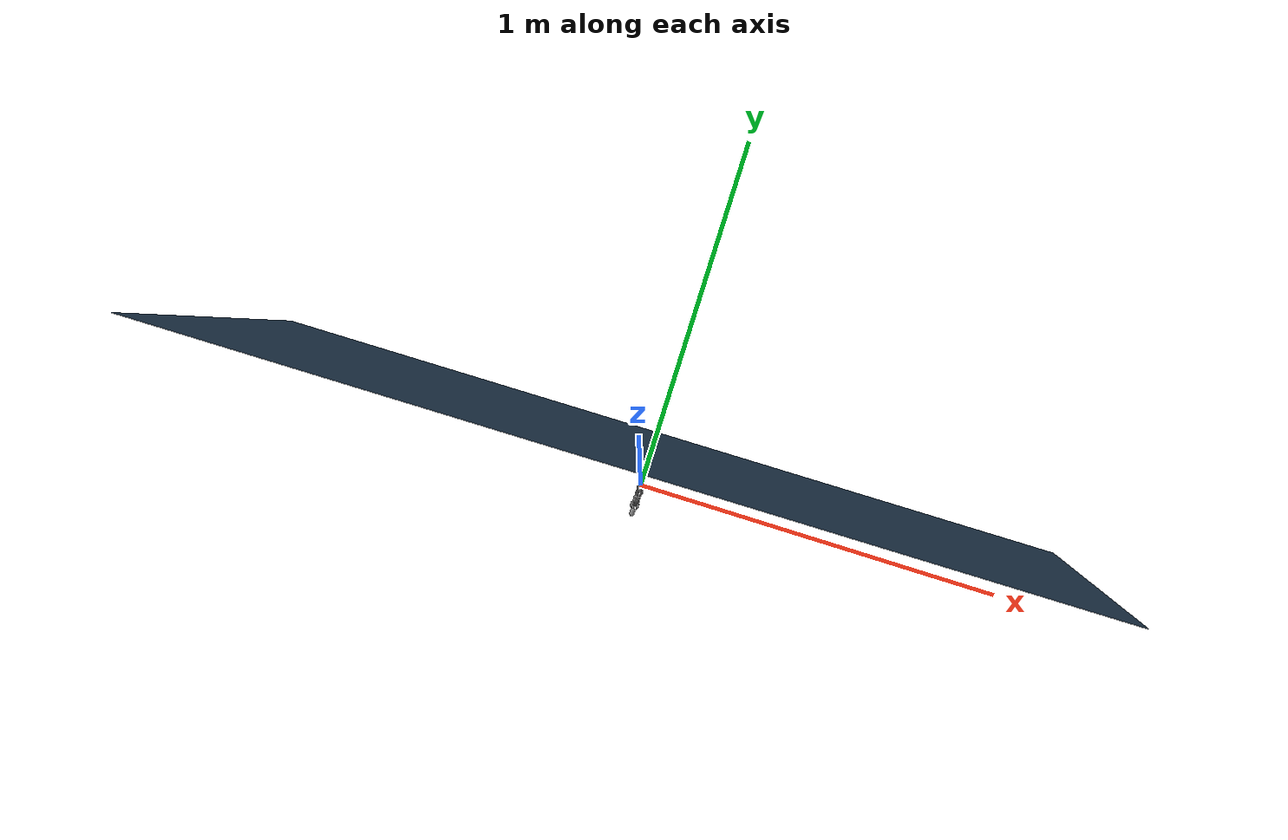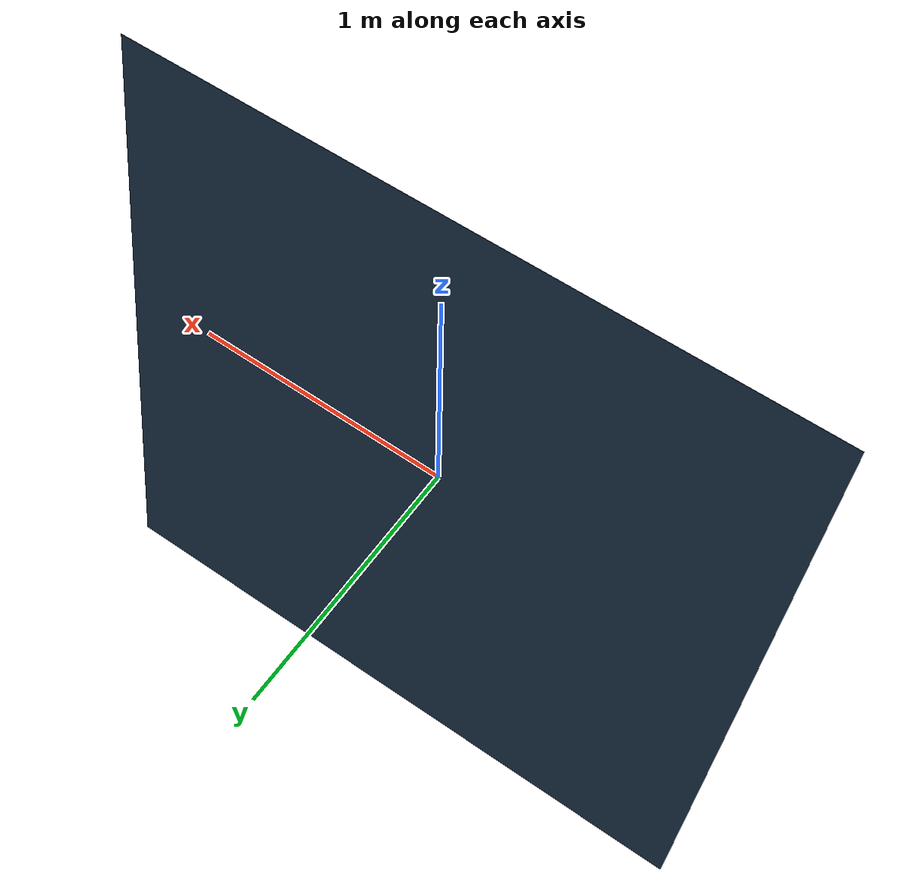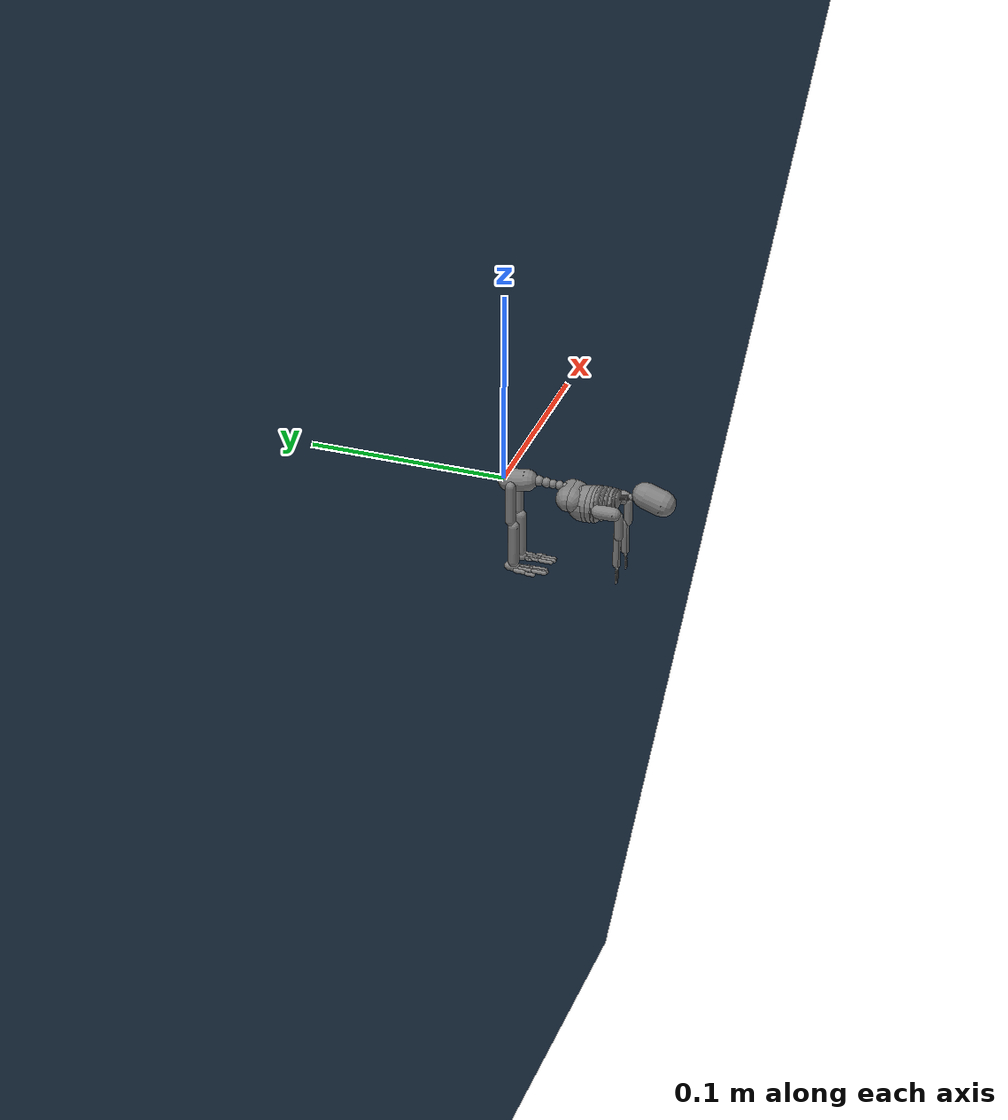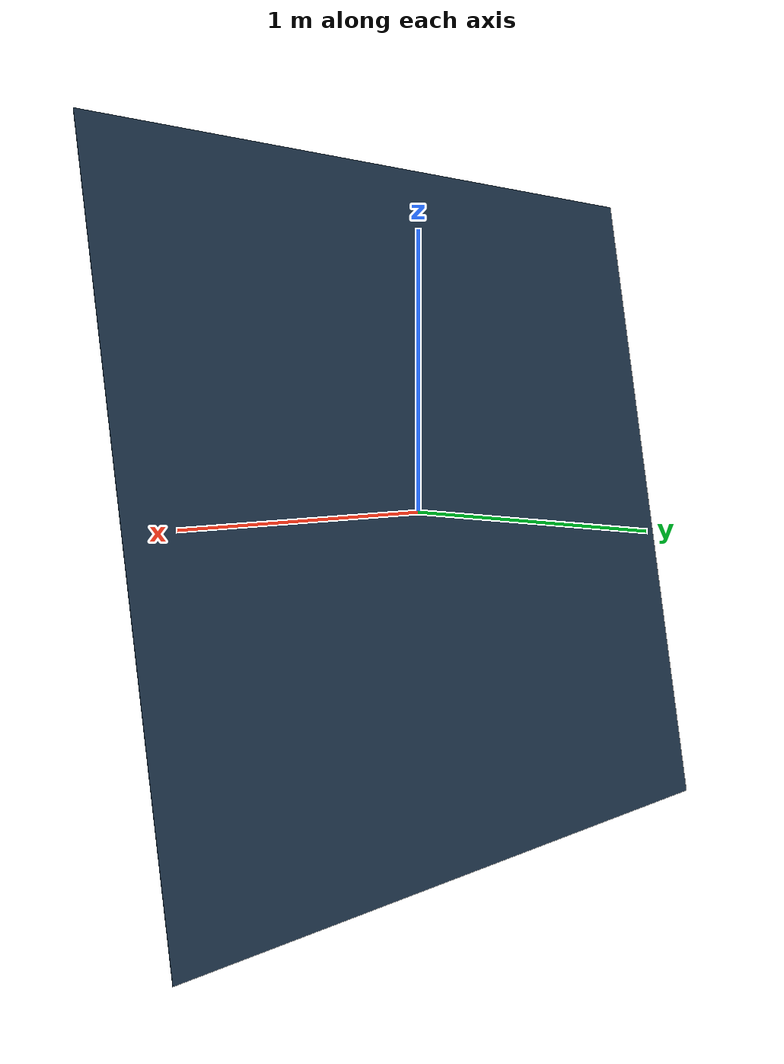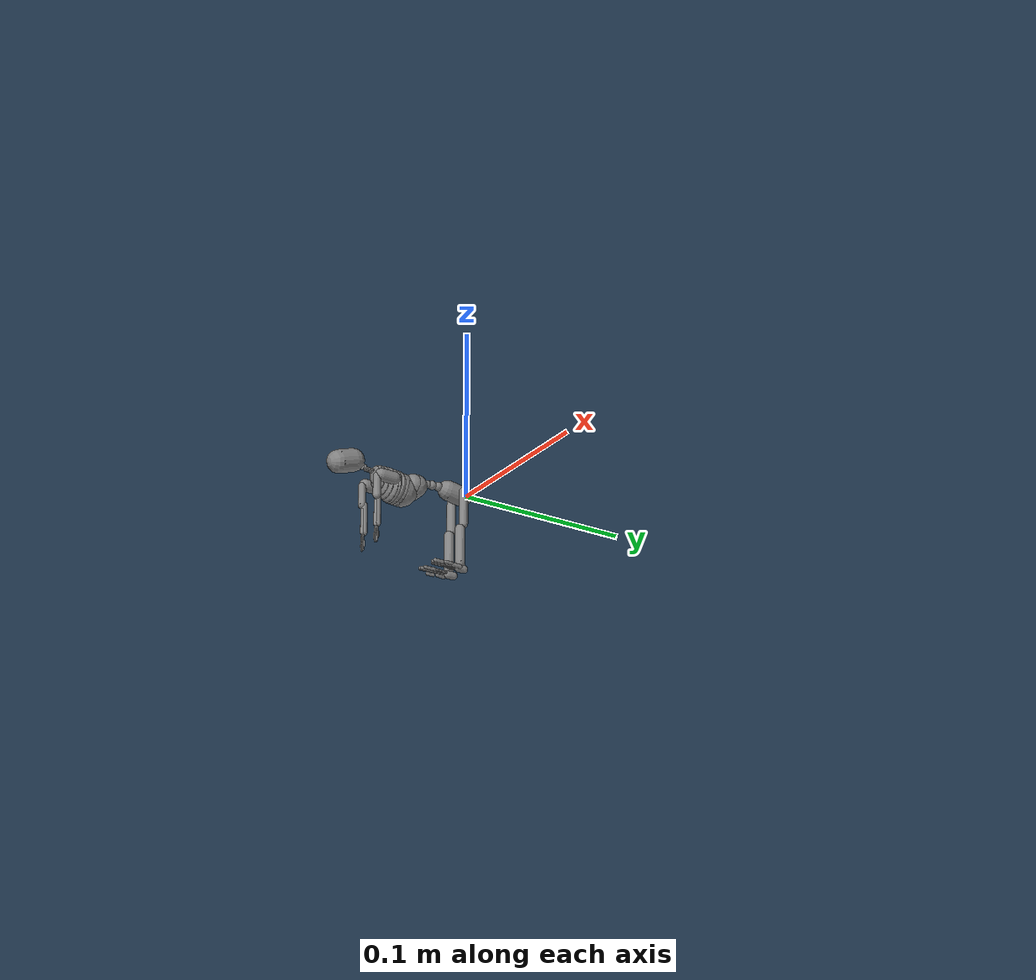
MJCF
<mujoco model="mouse">
  <compiler angle="radian" />
  <option>
    <flag contact="disable" />
  </option>
  <size njmax="500" nconmax="100" />
  <visual>
    <quality shadowsize="4096" />
    <global offwidth="1920" offheight="1200" elevation="-20" azimuth="120" />
  </visual>
  <asset>
    <texture type="skybox" builtin="gradient" rgb1="0 0 0" rgb2="0 0 0" width="32" height="512" />
    <texture name="body" type="cube" builtin="flat" mark="cross" width="128" height="128" rgb1="0.8 0.6 0.4" rgb2="0.8 0.6 0.4" markrgb="1 1 1" random="0.01" />
    <material name="body" texture="body" texuniform="true" rgba="0.8 0.6 .4 1" />
    <texture name="grid" type="2d" builtin="checker" width="512" height="200" rgb1=".1 .2 .3" rgb2=".2 .3 .4" />
    <material name="grid" texture="grid" texrepeat="10 10" texuniform="true" reflectance=".2" />
  </asset>
  <worldbody>
    <geom name="floor" contype="0" conaffinity="1" condim="3" pos="0 .1 0" zaxis="0.004 -.961 -.167" size="1.25 1.25 0.025" type="plane" material="grid" />
    <light name="spotlight" pos="0 -5 0" dir="0 1 0" diffuse=".8 .8 .8" specular=".4 .4 .4" directional="true" cutoff="45" exponent="20" />
    <body name="mouse" pos="0 0 0" quat="0 0 0 1">
      <freejoint name="root" />
      <geom pos="-4.19095e-09 0.00727621 0.000323871" type="capsule" size="0.00558884 0.00466261" quat="0.456701 0.539838 -0.539838 0.456701" />
      <body name="mouse__Lumbar6_interim_0" pos="0 0.01206 0.00074">
        <camera name="center_of_mass" mode="trackcom" pos="0 .05 -.25" xyaxes="-1 0 0 0 1 .1" />
        <inertial pos="0 0 0" mass="1e-06" diaginertia="1e-06 1e-06 1e-06" />
        <joint name="mouse__Lumbar6_bending" pos="0 0 0" axis="0 0 1" limited="true" range="-0.0872665 0.0872665" />
        <body name="mouse__Lumbar6_interim_1" pos="0 0 0">
          <inertial pos="0 0 0" mass="1e-06" diaginertia="1e-06 1e-06 1e-06" />
          <joint name="mouse__Lumbar6_rotation" pos="0 0 0" axis="0 1 0" limited="true" range="-0.0872665 0.0872665" />
          <body name="mouse__Lumbar6" pos="0 0 0">
            <inertial pos="0 0.00252 0.00133" quat="0.707107 0 0 0.707107" mass="0.000163962" diaginertia="1e-06 1e-06 1e-06" />
            <joint name="mouse__Lumbar6_flexion" pos="0 0 0" axis="1 0 0" limited="true" range="-0.10472 0.10472" />
            <geom pos="-4.5402e-09 0.00252485 0.00133634" type="sphere" size="0.00268279" />
            <body name="mouse__Lumbar5_interim_0" pos="0 0.00372 -3e-05">
              <inertial pos="0 0 0" mass="1e-06" diaginertia="1e-06 1e-06 1e-06" />
              <joint name="mouse__Lumbar5_bending" pos="0 0 0" axis="0 0 1" limited="true" range="-0.0872665 0.0872665" />
              <body name="mouse__Lumbar5_interim_1" pos="0 0 0">
                <inertial pos="0 0 0" mass="1e-06" diaginertia="1e-06 1e-06 1e-06" />
                <joint name="mouse__Lumbar5_rotation" pos="0 0 0" axis="0 1 0" limited="true" range="-0.0872665 0.0872665" />
                <body name="mouse__Lumbar5" pos="0 0 0">
                  <inertial pos="0 0.00237 0.00115" quat="0.707107 0 0 0.707107" mass="0.000137716" diaginertia="1e-06 1e-06 1e-06" />
                  <joint name="mouse__Lumbar5_flexion" pos="0 0 0" axis="1 0 0" limited="true" range="-0.10472 0.10472" />
                  <geom pos="-4.88944e-09 0.00237635 0.0011585" type="sphere" size="0.00260826" />
                  <body name="mouse__Lumbar4_interim_0" pos="0 0.00373 -2e-05">
                    <inertial pos="0 0 0" mass="1e-06" diaginertia="1e-06 1e-06 1e-06" />
                    <joint name="mouse__Lumbar4_bending" pos="0 0 0" axis="0 0 1" limited="true" range="-0.0872665 0.0872665" />
                    <body name="mouse__Lumbar4_interim_1" pos="0 0 0">
                      <inertial pos="0 0 0" mass="1e-06" diaginertia="1e-06 1e-06 1e-06" />
                      <joint name="mouse__Lumbar4_rotation" pos="0 0 0" axis="0 1 0" limited="true" range="-0.0872665 0.0872665" />
                      <body name="mouse__Lumbar4" pos="0 0 0">
                        <inertial pos="0 0.00244 0.00102" quat="0 0.707107 0 0.707107" mass="0.000120721" diaginertia="1e-06 1e-06 1e-06" />
                        <joint name="mouse__Lumbar4_flexion" pos="0 0 0" axis="1 0 0" limited="true" range="-0.10472 0.10472" />
                        <geom pos="-1.19908e-08 0.00244843 0.0010276" type="sphere" size="0.00248412" />
                        <body name="mouse__Lumbar3_interim_0" pos="0 0.00367 1e-05">
                          <inertial pos="0 0 0" mass="1e-06" diaginertia="1e-06 1e-06 1e-06" />
                          <joint name="mouse__Lumbar3_bending" pos="0 0 0" axis="0 0 1" limited="true" range="-0.0872665 0.0872665" />
                          <body name="mouse__Lumbar3_interim_1" pos="0 0 0">
                            <inertial pos="0 0 0" mass="1e-06" diaginertia="1e-06 1e-06 1e-06" />
                            <joint name="mouse__Lumbar3_rotation" pos="0 0 0" axis="0 1 0" limited="true" range="-0.0872665 0.0872665" />
                            <body name="mouse__Lumbar3" pos="0 0 0">
                              <inertial pos="0 0.00215 0.00076" quat="0 0.707107 0 0.707107" mass="8.5376e-05" diaginertia="1e-06 1e-06 1e-06" />
                              <joint name="mouse__Lumbar3_flexion" pos="0 0 0" axis="1 0 0" limited="true" range="-0.10472 0.10472" />
                              <geom pos="3.09665e-08 0.00215467 0.00076934" type="sphere" size="0.00221144" />
                              <body name="mouse__Lumbar2_interim_0" pos="0 0.00329 0">
                                <inertial pos="0 0 0" mass="1e-06" diaginertia="1e-06 1e-06 1e-06" />
                                <joint name="mouse__Lumbar2_bending" pos="0 0 0" axis="0 0 1" limited="true" range="-0.0872665 0.0872665" />
                                <body name="mouse__Lumbar2_interim_1" pos="0 0 0">
                                  <inertial pos="0 0 0" mass="1e-06" diaginertia="1e-06 1e-06 1e-06" />
                                  <joint name="mouse__Lumbar2_rotation" pos="0 0 0" axis="0 1 0" limited="true" range="-0.0872665 0.0872665" />
                                  <body name="mouse__Lumbar2" pos="0 0 0">
                                    <inertial pos="0 0.00237 0.00068" quat="0.5 0.5 -0.5 0.5" mass="8.17254e-05" diaginertia="1e-06 1e-06 1e-06" />
                                    <joint name="mouse__Lumbar2_flexion" pos="0 0 0" axis="1 0 0" limited="true" range="-0.10472 0.10472" />
                                    <geom pos="2.75904e-08 0.00237944 0.000683873" type="sphere" size="0.00228549" />
                                    <body name="mouse__Lumbar1_interim_0" pos="0 0.00334 -2e-05">
                                      <inertial pos="0 0 0" mass="1e-06" diaginertia="1e-06 1e-06 1e-06" />
                                      <joint name="mouse__Lumbar1_bending" pos="0 0 0" axis="0 0 1" limited="true" range="-0.0872665 0.0872665" />
                                      <body name="mouse__Lumbar1_interim_1" pos="0 0 0">
                                        <inertial pos="0 0 0" mass="1e-06" diaginertia="1e-06 1e-06 1e-06" />
                                        <joint name="mouse__Lumbar1_rotation" pos="0 0 0" axis="0 1 0" limited="true" range="-0.0872665 0.0872665" />
                                        <body name="mouse__Lumbar1" pos="0 0 0">
                                          <inertial pos="0 0.00185 0.00061" quat="0 0.707107 0 0.707107" mass="6.09118e-05" diaginertia="1e-06 1e-06 1e-06" />
                                          <joint name="mouse__Lumbar1_flexion" pos="0 0 0" axis="1 0 0" limited="true" range="-0.10472 0.10472" />
                                          <geom pos="2.99187e-08 0.0018565 0.000615176" type="sphere" size="0.00186689" />
                                          <body name="mouse__Thoracic13_interim_0" pos="0 0.00313 0">
                                            <inertial pos="0 0 0" mass="1e-06" diaginertia="1e-06 1e-06 1e-06" />
                                            <joint name="mouse__Thoracic13_bending" pos="0 0 0" axis="0 0 1" limited="true" range="-0.0872665 0.0872665" />
                                            <body name="mouse__Thoracic13_interim_1" pos="0 0 0">
                                              <inertial pos="0 0 0" mass="1e-06" diaginertia="1e-06 1e-06 1e-06" />
                                              <joint name="mouse__Thoracic13_rotation" pos="0 0 0" axis="0 1 0" limited="true" range="-0.0872665 0.0872665" />
                                              <body name="mouse__Thoracic13" pos="0 0 0">
                                                <inertial pos="0 0.00194 0.00048" quat="0 0.707107 0 0.707107" mass="5.4685e-05" diaginertia="1e-06 1e-06 1e-06" />
                                                <joint name="mouse__Thoracic13_flexion" pos="0 0 0" axis="1 0 0" limited="true" range="-0.0872665 0.0872665" />
                                                <geom pos="2.96859e-08 0.00194431 0.000488777" type="sphere" size="0.00193209" />
                                                <body name="mouse__Thoracic12_interim_0" pos="0 0.00264 0">
                                                  <inertial pos="0 0 0" mass="1e-06" diaginertia="1e-06 1e-06 1e-06" />
                                                  <joint name="mouse__Thoracic12_bending" pos="0 0 0" axis="0 0 1" limited="true" range="-0.0872665 0.0872665" />
                                                  <body name="mouse__Thoracic12_interim_1" pos="0 0 0">
                                                    <inertial pos="0 0 0" mass="1e-06" diaginertia="1e-06 1e-06 1e-06" />
                                                    <joint name="mouse__Thoracic12_rotation" pos="0 0 0" axis="0 1 0" limited="true" range="-0.0872665 0.0872665" />
                                                    <body name="mouse__Thoracic12" pos="0 0 0">
                                                      <inertial pos="0 -0.00096 -0.00395" quat="0.5 0.5 0.5 0.5" mass="0.00187536" diaginertia="1e-06 1e-06 1e-06" />
                                                      <joint name="mouse__Thoracic12_flexion" pos="0 0 0" axis="1 0 0" limited="true" range="-0.0872665 0.0872665" />
                                                      <geom pos="4.28408e-08 -0.000964784 -0.00395056" type="capsule" size="0.0064722 0.00350613" quat="0.5 0.5 0.5 0.5" />
                                                      <body name="mouse__Thoracic11_interim_0" pos="0 0.00198 -2e-05">
                                                        <inertial pos="0 0 0" mass="1e-06" diaginertia="1e-06 1e-06 1e-06" />
                                                        <joint name="mouse__Thoracic11_bending" pos="0 0 0" axis="0 0 1" limited="true" range="-0.0872665 0.0872665" />
                                                        <body name="mouse__Thoracic11_interim_1" pos="0 0 0">
                                                          <inertial pos="0 0 0" mass="1e-06" diaginertia="1e-06 1e-06 1e-06" />
                                                          <joint name="mouse__Thoracic11_rotation" pos="0 0 0" axis="0 1 0" limited="true" range="-0.0872665 0.0872665" />
                                                          <body name="mouse__Thoracic11" pos="0 0 0">
                                                            <inertial pos="0 -0.00117 -0.00389" quat="0.5 0.5 0.5 0.5" mass="0.00198397" diaginertia="1e-06 1e-06 1e-06" />
                                                            <joint name="mouse__Thoracic11_flexion" pos="0 0 0" axis="1 0 0" limited="true" range="-0.0872665 0.0872665" />
                                                            <geom pos="4.19095e-08 -0.00117255 -0.00389368" type="capsule" size="0.00627723 0.0037011" quat="0.5 0.5 0.5 0.5" />
                                                            <body name="mouse__Thoracic10_interim_0" pos="0 0.00199 -2e-05">
                                                              <inertial pos="0 0 0" mass="1e-06" diaginertia="1e-06 1e-06 1e-06" />
                                                              <joint name="mouse__Thoracic10_bending" pos="0 0 0" axis="0 0 1" limited="true" range="-0.0872665 0.0872665" />
                                                              <body name="mouse__Thoracic10_interim_1" pos="0 0 0">
                                                                <inertial pos="0 0 0" mass="1e-06" diaginertia="1e-06 1e-06 1e-06" />
                                                                <joint name="mouse__Thoracic10_rotation" pos="0 0 0" axis="0 1 0" limited="true" range="-0.0872665 0.0872665" />
                                                                <body name="mouse__Thoracic10" pos="0 0 0">
                                                                  <inertial pos="0 0.00214 -0.00697" quat="0.5 0.5 0.5 0.5" mass="0.00422641" diaginertia="1e-06 1e-06 1e-06" />
                                                                  <joint name="mouse__Thoracic10_flexion" pos="0 0 0" axis="1 0 0" limited="true" range="-0.0872665 0.0872665" />
                                                                  <geom pos="-6.0536e-09 0.00214743 -0.00697063" type="sphere" size="0.00911416" />
                                                                  <body name="mouse__Thoracic9_interim_0" pos="0 0.00206 -1e-05">
                                                                    <inertial pos="0 0 0" mass="1e-06" diaginertia="1e-06 1e-06 1e-06" />
                                                                    <joint name="mouse__Thoracic9_bending" pos="0 0 0" axis="0 0 1" limited="true" range="-0.0872665 0.0872665" />
                                                                    <body name="mouse__Thoracic9_interim_1" pos="0 0 0">
                                                                      <inertial pos="0 0 0" mass="1e-06" diaginertia="1e-06 1e-06 1e-06" />
                                                                      <joint name="mouse__Thoracic9_rotation" pos="0 0 0" axis="0 1 0" limited="true" range="-0.0872665 0.0872665" />
                                                                      <body name="mouse__Thoracic9" pos="0 0 0">
                                                                        <inertial pos="0 0.00162 -0.00669" quat="0.5 0.5 0.5 0.5" mass="0.00365901" diaginertia="1e-06 1e-06 1e-06" />
                                                                        <joint name="mouse__Thoracic9_flexion" pos="0 0 0" axis="1 0 0" limited="true" range="-0.0872665 0.0872665" />
                                                                        <geom pos="-3.77186e-08 0.00162178 -0.00669017" type="sphere" size="0.00922135" />
                                                                        <body name="mouse__Thoracic8_interim_0" pos="0 0.00203 0">
                                                                          <inertial pos="0 0 0" mass="1e-06" diaginertia="1e-06 1e-06 1e-06" />
                                                                          <joint name="mouse__Thoracic8_bending" pos="0 0 0" axis="0 0 1" limited="true" range="-0.0872665 0.0872665" />
                                                                          <body name="mouse__Thoracic8_interim_1" pos="0 0 0">
                                                                            <inertial pos="0 0 0" mass="1e-06" diaginertia="1e-06 1e-06 1e-06" />
                                                                            <joint name="mouse__Thoracic8_rotation" pos="0 0 0" axis="0 1 0" limited="true" range="-0.0872665 0.0872665" />
                                                                            <body name="mouse__Thoracic8" pos="0 0 0">
                                                                              <inertial pos="0 0.0021 -0.0064" quat="0.5 0.5 0.5 0.5" mass="0.00302533" diaginertia="1e-06 1e-06 1e-06" />
                                                                              <joint name="mouse__Thoracic8_flexion" pos="0 0 0" axis="1 0 0" limited="true" range="-0.0872665 0.0872665" />
                                                                              <geom pos="2.00234e-08 0.00210878 -0.00640541" type="ellipsoid" size="0.00407479 0.0100135 0.0092681" quat="0.707107 0 0 0.707107" />
                                                                              <body name="mouse__Thoracic7_interim_0" pos="0 0.00206 0">
                                                                                <inertial pos="0 0 0" mass="1e-06" diaginertia="1e-06 1e-06 1e-06" />
                                                                                <joint name="mouse__Thoracic7_bending" pos="0 0 0" axis="0 0 1" limited="true" range="-0.0872665 0.0872665" />
                                                                                <body name="mouse__Thoracic7_interim_1" pos="0 0 0">
                                                                                  <inertial pos="0 0 0" mass="1e-06" diaginertia="1e-06 1e-06 1e-06" />
                                                                                  <joint name="mouse__Thoracic7_rotation" pos="0 0 0" axis="0 1 0" limited="true" range="-0.0872665 0.0872665" />
                                                                                  <body name="mouse__Thoracic7" pos="0 0 0">
                                                                                    <inertial pos="0 0.00201 -0.00613" quat="0.5 0.5 0.5 0.5" mass="0.00221615" diaginertia="1e-06 1e-06 1e-06" />
                                                                                    <joint name="mouse__Thoracic7_flexion" pos="0 0 0" axis="1 0 0" limited="true" range="-0.0872665 0.0872665" />
                                                                                    <geom pos="1.87661e-07 0.00201215 -0.00613619" type="ellipsoid" size="0.0029898 0.00997371 0.00928991" quat="0.707107 0 0 0.707107" />
                                                                                    <body name="mouse__Thoracic6_interim_0" pos="0 0.00205 0">
                                                                                      <inertial pos="0 0 0" mass="1e-06" diaginertia="1e-06 1e-06 1e-06" />
                                                                                      <joint name="mouse__Thoracic6_bending" pos="0 0 0" axis="0 0 1" limited="true" range="-0.0872665 0.0872665" />
                                                                                      <body name="mouse__Thoracic6_interim_1" pos="0 0 0">
                                                                                        <inertial pos="0 0 0" mass="1e-06" diaginertia="1e-06 1e-06 1e-06" />
                                                                                        <joint name="mouse__Thoracic6_rotation" pos="0 0 0" axis="0 1 0" limited="true" range="-0.0872665 0.0872665" />
                                                                                        <body name="mouse__Thoracic6" pos="0 0 0">
                                                                                          <inertial pos="0 0.00125 -0.00592" quat="0.5 0.5 0.5 0.5" mass="0.00169488" diaginertia="1e-06 1e-06 1e-06" />
                                                                                          <joint name="mouse__Thoracic6_flexion" pos="0 0 0" axis="1 0 0" limited="true" range="-0.0872665 0.0872665" />
                                                                                          <geom pos="-1.88593e-07 0.00125737 -0.00592692" type="ellipsoid" size="0.00238927 0.00962444 0.00921314" quat="0.707107 0 0 0.707107" />
                                                                                          <body name="mouse__Thoracic5_interim_0" pos="0 0.00206 0">
                                                                                            <inertial pos="0 0 0" mass="1e-06" diaginertia="1e-06 1e-06 1e-06" />
                                                                                            <joint name="mouse__Thoracic5_bending" pos="0 0 0" axis="0 0 1" limited="true" range="-0.0872665 0.0872665" />
                                                                                            <body name="mouse__Thoracic5_interim_1" pos="0 0 0">
                                                                                              <inertial pos="0 0 0" mass="1e-06" diaginertia="1e-06 1e-06 1e-06" />
                                                                                              <joint name="mouse__Thoracic5_rotation" pos="0 0 0" axis="0 1 0" limited="true" range="-0.0872665 0.0872665" />
                                                                                              <body name="mouse__Thoracic5" pos="0 0 0">
                                                                                                <inertial pos="0 0.00171 -0.00514" quat="0.5 0.5 0.5 0.5" mass="0.00123608" diaginertia="1e-06 1e-06 1e-06" />
                                                                                                <joint name="mouse__Thoracic5_flexion" pos="0 0 0" axis="1 0 0" limited="true" range="-0.0872665 0.0872665" />
                                                                                                <geom pos="3.10596e-07 0.00171411 -0.00514142" type="ellipsoid" size="0.00192082 0.00905096 0.00888743" quat="0.707107 0 0 0.707107" />
                                                                                                <body name="mouse__Thoracic4_interim_0" pos="0 0.00203 0">
                                                                                                  <inertial pos="0 0 0" mass="1e-06" diaginertia="1e-06 1e-06 1e-06" />
                                                                                                  <joint name="mouse__Thoracic4_bending" pos="0 0 0" axis="0 0 1" limited="true" range="-0.0872665 0.0872665" />
                                                                                                  <body name="mouse__Thoracic4_interim_1" pos="0 0 0">
                                                                                                    <inertial pos="0 0 0" mass="1e-06" diaginertia="1e-06 1e-06 1e-06" />
                                                                                                    <joint name="mouse__Thoracic4_rotation" pos="0 0 0" axis="0 1 0" limited="true" range="-0.0872665 0.0872665" />
                                                                                                    <body name="mouse__Thoracic4" pos="0 0 0">
                                                                                                      <inertial pos="0 0.00195 -0.00438" quat="0.707107 0 0 0.707107" mass="0.000979661" diaginertia="1e-06 1e-06 1e-06" />
                                                                                                      <joint name="mouse__Thoracic4_flexion" pos="0 0 0" axis="1 0 0" limited="true" range="-0.0872665 0.0872665" />
                                                                                                      <geom pos="6.45407e-07 0.00195623 -0.00438332" type="ellipsoid" size="0.00192297 0.007645 0.00832983" quat="0.707107 0 0 0.707107" />
                                                                                                      <body name="mouse__Thoracic3_interim_0" pos="0 0.00206 1e-05">
                                                                                                        <inertial pos="0 0 0" mass="1e-06" diaginertia="1e-06 1e-06 1e-06" />
                                                                                                        <joint name="mouse__Thoracic3_bending" pos="0 0 0" axis="0 0 1" limited="true" range="-0.0872665 0.0872665" />
                                                                                                        <body name="mouse__Thoracic3_interim_1" pos="0 0 0">
                                                                                                          <inertial pos="0 0 0" mass="1e-06" diaginertia="1e-06 1e-06 1e-06" />
                                                                                                          <joint name="mouse__Thoracic3_rotation" pos="0 0 0" axis="0 1 0" limited="true" range="-0.0872665 0.0872665" />
                                                                                                          <body name="mouse__Thoracic3" pos="0 0 0">
                                                                                                            <inertial pos="0 0.0021 -0.00342" quat="0.707107 0 0 0.707107" mass="0.000820796" diaginertia="1e-06 1e-06 1e-06" />
                                                                                                            <joint name="mouse__Thoracic3_flexion" pos="0 0 0" axis="1 0 0" limited="true" range="-0.0872665 0.0872665" />
                                                                                                            <geom pos="-4.23752e-08 0.00210047 -0.0034247" type="ellipsoid" size="0.00204857 0.00681174 0.00735252" quat="0.707107 0 0 0.707107" />
                                                                                                            <body name="mouse__Thoracic2_interim_0" pos="0 0.00198 3e-05">
                                                                                                              <inertial pos="0 0 0" mass="1e-06" diaginertia="1e-06 1e-06 1e-06" />
                                                                                                              <joint name="mouse__Thoracic2_bending" pos="0 0 0" axis="0 0 1" limited="true" range="-0.0872665 0.0872665" />
                                                                                                              <body name="mouse__Thoracic2_interim_1" pos="0 0 0">
                                                                                                                <inertial pos="0 0 0" mass="1e-06" diaginertia="1e-06 1e-06 1e-06" />
                                                                                                                <joint name="mouse__Thoracic2_rotation" pos="0 0 0" axis="0 1 0" limited="true" range="-0.0872665 0.0872665" />
                                                                                                                <body name="mouse__Thoracic2" pos="0 0 0">
                                                                                                                  <inertial pos="0 0.00146 -0.00253" quat="0.707107 0 0 0.707107" mass="0.000449683" diaginertia="1e-06 1e-06 1e-06" />
                                                                                                                  <joint name="mouse__Thoracic2_flexion" pos="0 0 0" axis="1 0 0" limited="true" range="-0.0872665 0.0872665" />
                                                                                                                  <geom pos="7.1805e-07 0.00146501 -0.00253801" type="ellipsoid" size="0.00618292 0.00143575 0.00633206" quat="1 0 0 0" />
                                                                                                                  <body name="mouse__Thoracic1_interim_0" pos="0 0.00195 4e-05">
                                                                                                                    <inertial pos="0 0 0" mass="1e-06" diaginertia="1e-06 1e-06 1e-06" />
                                                                                                                    <joint name="mouse__Thoracic1_bending" pos="0 0 0" axis="0 0 1" limited="true" range="-0.0872665 0.0872665" />
                                                                                                                    <body name="mouse__Thoracic1_interim_1" pos="0 0 0">
                                                                                                                      <inertial pos="0 0 0" mass="1e-06" diaginertia="1e-06 1e-06 1e-06" />
                                                                                                                      <joint name="mouse__Thoracic1_rotation" pos="0 0 0" axis="0 1 0" limited="true" range="-0.0872665 0.0872665" />
                                                                                                                      <body name="mouse__Thoracic1" pos="0 0 0">
                                                                                                                        <inertial pos="0 0.00073 -0.00175" quat="0.707107 0 0 0.707107" mass="0.000247848" diaginertia="1e-06 1e-06 1e-06" />
                                                                                                                        <joint name="mouse__Thoracic1_flexion" pos="0 0 0" axis="1 0 0" limited="true" range="-0.0872665 0.0872665" />
                                                                                                                        <geom pos="-1.14087e-08 0.000736896 -0.00175104" type="ellipsoid" size="0.00471121 0.00133871 0.00491221" quat="1 0 0 0" />
                                                                                                                        <body name="mouse__Cervical8_interim_0" pos="0 0.00199 4e-05">
                                                                                                                          <inertial pos="0 0 0" mass="1e-06" diaginertia="1e-06 1e-06 1e-06" />
                                                                                                                          <joint name="mouse__Cervical8_bending" pos="0 0 0" axis="0 0 1" limited="true" range="-0.0872665 0.0872665" />
                                                                                                                          <body name="mouse__Cervical8_interim_1" pos="0 0 0">
                                                                                                                            <inertial pos="0 0 0" mass="1e-06" diaginertia="1e-06 1e-06 1e-06" />
                                                                                                                            <joint name="mouse__Cervical8_rotation" pos="0 0 0" axis="0 1 0" limited="true" range="-0.0872665 0.0872665" />
                                                                                                                            <body name="mouse__Cervical8" pos="0 0 0">
                                                                                                                              <inertial pos="0 0.00042 -5e-05" quat="0.5 0.5 0.5 0.5" mass="8.61405e-06" diaginertia="1e-06 1e-06 1e-06" />
                                                                                                                              <joint name="mouse__Cervical8_flexion" pos="0 0 0" axis="1 0 0" limited="true" range="-0.15708 0.15708" />
                                                                                                                              <geom pos="-7.82893e-08 0.000423398 -5.63485e-05" type="ellipsoid" size="0.00177559 0.000488602 0.00124114" quat="1 0 0 0" />
                                                                                                                              <body name="mouse__Cervical7_interim_0" pos="0 0.00089 1e-05">
                                                                                                                                <inertial pos="0 0 0" mass="1e-06" diaginertia="1e-06 1e-06 1e-06" />
                                                                                                                                <joint name="mouse__Cervical7_bending" pos="0 0 0" axis="0 0 1" limited="true" range="-0.0872665 0.0872665" />
                                                                                                                                <body name="mouse__Cervical7_interim_1" pos="0 0 0">
                                                                                                                                  <inertial pos="0 0 0" mass="1e-06" diaginertia="1e-06 1e-06 1e-06" />
                                                                                                                                  <joint name="mouse__Cervical7_rotation" pos="0 0 0" axis="0 1 0" limited="true" range="-0.0872665 0.0872665" />
                                                                                                                                  <body name="mouse__Cervical7" pos="0 0 0">
                                                                                                                                    <inertial pos="0 0.0004 5e-05" quat="0.5 0.5 0.5 0.5" mass="8.42975e-06" diaginertia="1e-06 1e-06 1e-06" />
                                                                                                                                    <joint name="mouse__Cervical7_flexion" pos="0 0 0" axis="1 0 0" limited="true" range="-0.15708 0.15708" />
                                                                                                                                    <geom pos="-1.42708e-06 0.000403509 5.051e-05" type="ellipsoid" size="0.00177803 0.000482451 0.00122838" quat="1 0 0 0" />
                                                                                                                                    <body name="mouse__Cervical6_interim_0" pos="0 0.00086 1e-05">
                                                                                                                                      <inertial pos="0 0 0" mass="1e-06" diaginertia="1e-06 1e-06 1e-06" />
                                                                                                                                      <joint name="mouse__Cervical6_bending" pos="0 0 0" axis="0 0 1" limited="true" range="-0.0872665 0.0872665" />
                                                                                                                                      <body name="mouse__Cervical6_interim_1" pos="0 0 0">
                                                                                                                                        <inertial pos="0 0 0" mass="1e-06" diaginertia="1e-06 1e-06 1e-06" />
                                                                                                                                        <joint name="mouse__Cervical6_rotation" pos="0 0 0" axis="0 1 0" limited="true" range="-0.0872665 0.0872665" />
                                                                                                                                        <body name="mouse__Cervical6" pos="0 0 0">
                                                                                                                                          <inertial pos="0 0.00039 0.0001" quat="0.5 0.5 0.5 0.5" mass="8.28884e-06" diaginertia="1e-06 1e-06 1e-06" />
                                                                                                                                          <joint name="mouse__Cervical6_flexion" pos="0 0 0" axis="1 0 0" limited="true" range="-0.15708 0.15708" />
                                                                                                                                          <geom pos="4.62751e-08 0.000396628 0.00010558" type="ellipsoid" size="0.00177183 0.000474587 0.00123216" quat="1 0 0 0" />
                                                                                                                                          <body name="mouse__Cervical5_interim_0" pos="0 0.00083 1e-05">
                                                                                                                                            <inertial pos="0 0 0" mass="1e-06" diaginertia="1e-06 1e-06 1e-06" />
                                                                                                                                            <joint name="mouse__Cervical5_bending" pos="0 0 0" axis="0 0 1" limited="true" range="-0.0872665 0.0872665" />
                                                                                                                                            <body name="mouse__Cervical5_interim_1" pos="0 0 0">
                                                                                                                                              <inertial pos="0 0 0" mass="1e-06" diaginertia="1e-06 1e-06 1e-06" />
                                                                                                                                              <joint name="mouse__Cervical5_rotation" pos="0 0 0" axis="0 1 0" limited="true" range="-0.0872665 0.0872665" />
                                                                                                                                              <body name="mouse__Cervical5" pos="0 0 0">
                                                                                                                                                <inertial pos="0 0.00041 0.00013" quat="0.5 0.5 0.5 0.5" mass="8.21986e-06" diaginertia="1e-06 1e-06 1e-06" />
                                                                                                                                                <joint name="mouse__Cervical5_flexion" pos="0 0 0" axis="1 0 0" limited="true" range="-0.15708 0.15708" />
                                                                                                                                                <geom pos="4.43542e-08 0.00041713 0.000131472" type="ellipsoid" size="0.0017772 0.000474928 0.00121733" quat="1 0 0 0" />
                                                                                                                                                <body name="mouse__Cervical4_interim_0" pos="0 0.00081 1e-05">
                                                                                                                                                  <inertial pos="0 0 0" mass="1e-06" diaginertia="1e-06 1e-06 1e-06" />
                                                                                                                                                  <joint name="mouse__Cervical4_bending" pos="0 0 0" axis="0 0 1" limited="true" range="-0.0872665 0.0872665" />
                                                                                                                                                  <body name="mouse__Cervical4_interim_1" pos="0 0 0">
                                                                                                                                                    <inertial pos="0 0 0" mass="1e-06" diaginertia="1e-06 1e-06 1e-06" />
                                                                                                                                                    <joint name="mouse__Cervical4_rotation" pos="0 0 0" axis="0 1 0" limited="true" range="-0.0872665 0.0872665" />
                                                                                                                                                    <body name="mouse__Cervical4" pos="0 0 0">
                                                                                                                                                      <inertial pos="0 0.00038 0.00015" quat="0.5 0.5 0.5 0.5" mass="8.56537e-06" diaginertia="1e-06 1e-06 1e-06" />
                                                                                                                                                      <joint name="mouse__Cervical4_flexion" pos="0 0 0" axis="1 0 0" limited="true" range="-0.15708 0.15708" />
                                                                                                                                                      <geom pos="-8.14907e-10 0.000384785 0.000158546" type="ellipsoid" size="0.00177536 0.00048697 0.00123842" quat="1 0 0 0" />
                                                                                                                                                      <body name="mouse__Cervical3_interim_0" pos="0 0.00086 0">
                                                                                                                                                        <inertial pos="0 0 0" mass="1e-06" diaginertia="1e-06 1e-06 1e-06" />
                                                                                                                                                        <joint name="mouse__Cervical3_bending" pos="0 0 0" axis="0 0 1" limited="true" range="-0.0872665 0.0872665" />
                                                                                                                                                        <body name="mouse__Cervical3_interim_1" pos="0 0 0">
                                                                                                                                                          <inertial pos="0 0 0" mass="1e-06" diaginertia="1e-06 1e-06 1e-06" />
                                                                                                                                                          <joint name="mouse__Cervical3_rotation" pos="0 0 0" axis="0 1 0" limited="true" range="-0.0872665 0.0872665" />
                                                                                                                                                          <body name="mouse__Cervical3" pos="0 0 0">
                                                                                                                                                            <inertial pos="0 0.00033 0.00017" quat="0.5 0.5 0.5 0.5" mass="8.43003e-06" diaginertia="1e-06 1e-06 1e-06" />
                                                                                                                                                            <joint name="mouse__Cervical3_flexion" pos="0 0 0" axis="1 0 0" limited="true" range="-0.15708 0.15708" />
                                                                                                                                                            <geom pos="-1.80444e-09 0.000332344 0.000174581" type="ellipsoid" size="0.00177684 0.000482183 0.00122993" quat="1 0 0 0" />
                                                                                                                                                            <body name="mouse__Cervical2_interim_0" pos="0 0.00081 0">
                                                                                                                                                              <inertial pos="0 0 0" mass="1e-06" diaginertia="1e-06 1e-06 1e-06" />
                                                                                                                                                              <joint name="mouse__Cervical2_bending" pos="0 0 0" axis="0 0 1" limited="true" range="-0.0872665 0.0872665" />
                                                                                                                                                              <body name="mouse__Cervical2_interim_1" pos="0 0 0">
                                                                                                                                                                <inertial pos="0 0 0" mass="1e-06" diaginertia="1e-06 1e-06 1e-06" />
                                                                                                                                                                <joint name="mouse__Cervical2_rotation" pos="0 0 0" axis="0 1 0" limited="true" range="-0.0872665 0.0872665" />
                                                                                                                                                                <body name="mouse__Cervical2" pos="0 0 0">
                                                                                                                                                                  <inertial pos="0 0.00043 0.001" quat="0.707107 0 0 0.707107" mass="3.51285e-05" diaginertia="1e-06 1e-06 1e-06" />
                                                                                                                                                                  <joint name="mouse__Cervical2_flexion" pos="0 0 0" axis="1 0 0" limited="true" range="-0.15708 0.15708" />
                                                                                                                                                                  <geom pos="2.44472e-09 0.000435758 0.00100044" type="sphere" size="0.00163232" />
                                                                                                                                                                  <body name="mouse__Cervical1_interim_0" pos="0 0.00113 2e-05">
                                                                                                                                                                    <inertial pos="0 0 0" mass="1e-06" diaginertia="1e-06 1e-06 1e-06" />
                                                                                                                                                                    <joint name="mouse__Cervical1_bending" pos="0 0 0" axis="0 0 1" limited="true" range="-0.0872665 0.0872665" />
                                                                                                                                                                    <body name="mouse__Cervical1_interim_1" pos="0 0 0">
                                                                                                                                                                      <inertial pos="0 0 0" mass="1e-06" diaginertia="1e-06 1e-06 1e-06" />
                                                                                                                                                                      <joint name="mouse__Cervical1_rotation" pos="0 0 0" axis="0 1 0" limited="true" range="-0.0872665 0.0872665" />
                                                                                                                                                                      <body name="mouse__Cervical1" pos="0 0 0">
                                                                                                                                                                        <inertial pos="0 0.00036 0.0004" quat="0.5 0.5 0.5 0.5" mass="9.13264e-06" diaginertia="1e-06 1e-06 1e-06" />
                                                                                                                                                                        <joint name="mouse__Cervical1_flexion" pos="0 0 0" axis="1 0 0" limited="true" range="-0.15708 0.15708" />
                                                                                                                                                                        <geom pos="2.57278e-08 0.000360794 0.000402471" type="ellipsoid" size="0.00160361 0.000554994 0.00128268" quat="1 0 0 0" />
                                                                                                                                                                        <body name="mouse__Head_interim_0" pos="0 0.00085 2e-05">
                                                                                                                                                                          <inertial pos="0 0 0" mass="1e-06" diaginertia="1e-06 1e-06 1e-06" />
                                                                                                                                                                          <joint name="mouse__Head_adduction" pos="0 0 0" axis="0 0 1" limited="true" range="-0.174533 0.174533" />
                                                                                                                                                                          <body name="mouse__Head_interim_1" pos="0 0 0">
                                                                                                                                                                            <inertial pos="0 0 0" mass="1e-06" diaginertia="1e-06 1e-06 1e-06" />
                                                                                                                                                                            <joint name="mouse__Head_rotation" pos="0 0 0" axis="0 1 0" limited="true" range="-0.174533 0.174533" />
                                                                                                                                                                            <body name="mouse__Head" pos="0 0 0">
                                                                                                                                                                              <inertial pos="0 0.01046 0.00191" quat="0.707107 0.707107 0 0" mass="0.00403045" diaginertia="1e-06 1e-06 1e-06" />
                                                                                                                                                                              <joint name="mouse__Head_flexion" pos="0 0 0" axis="1 0 0" limited="true" range="-0.174533 0.174533" />
                                                                                                                                                                              <geom pos="6.72881e-08 0.0101666 0.00181757" type="capsule" size="0.00655278 0.00470617" quat="0.810958 0.585104 0 0" />
                                                                                                                                                                            </body>
                                                                                                                                                                          </body>
                                                                                                                                                                        </body>
                                                                                                                                                                      </body>
                                                                                                                                                                    </body>
                                                                                                                                                                  </body>
                                                                                                                                                                </body>
                                                                                                                                                              </body>
                                                                                                                                                            </body>
                                                                                                                                                          </body>
                                                                                                                                                        </body>
                                                                                                                                                      </body>
                                                                                                                                                    </body>
                                                                                                                                                  </body>
                                                                                                                                                </body>
                                                                                                                                              </body>
                                                                                                                                            </body>
                                                                                                                                          </body>
                                                                                                                                        </body>
                                                                                                                                      </body>
                                                                                                                                    </body>
                                                                                                                                  </body>
                                                                                                                                </body>
                                                                                                                              </body>
                                                                                                                            </body>
                                                                                                                          </body>
                                                                                                                        </body>
                                                                                                                        <body name="mouse__LScapula" pos="-0.00687 0.00335 -0.00575">
                                                                                                                          <inertial pos="-0.00162 -0.00587 0.00058" quat="0.707107 0.707107 0 0" mass="0.000444827" diaginertia="1e-06 1e-06 1e-06" />
                                                                                                                          <joint name="mouse__LScapula_rotation" pos="0 0 0" axis="0 0 1" limited="true" range="-0.174533 0.174533" />
                                                                                                                          <geom pos="-0.0016227 -0.00587866 0.000587147" type="capsule" size="0.00352563 0.00407038" quat="0.707107 -0.707107 0 0" />
                                                                                                                          <body name="mouse__LHumerus_interim_0" pos="0 0 0">
                                                                                                                            <inertial pos="0 0 0" mass="1e-06" diaginertia="1e-06 1e-06 1e-06" />
                                                                                                                            <joint name="mouse__LShoulder_rotation" pos="0 0 0" axis="0 0 1" limited="true" range="-0.0523599 0.628319" />
                                                                                                                            <body name="mouse__LHumerus_interim_1" pos="0 0 0">
                                                                                                                              <inertial pos="0 0 0" mass="1e-06" diaginertia="1e-06 1e-06 1e-06" />
                                                                                                                              <joint name="mouse__LShoulder_adduction" pos="0 0 0" axis="0 1 0" limited="true" range="-0.244346 0.698132" />
                                                                                                                              <body name="mouse__LHumerus" pos="0 0 0">
                                                                                                                                <inertial pos="-0.00091 0.00049 -0.00632" mass="0.000245766" diaginertia="1e-06 1e-06 1e-06" />
                                                                                                                                <joint name="mouse__LShoulder_flexion" pos="0 0 0" axis="1 0 0" limited="true" range="-0.785398 0.785398" />
                                                                                                                                <geom pos="-0.000919295 0.000490161 -0.00631997" type="capsule" size="0.0021606 0.00568261" quat="1 0 0 0" />
                                                                                                                                <body name="mouse__LUlna" pos="9e-05 0.00015 -0.01337">
                                                                                                                                  <inertial pos="-0.00027 -0.00079 -0.00691" mass="0.000139187" diaginertia="1e-06 1e-06 1e-06" />
                                                                                                                                  <joint name="mouse__LElbow_flexion" pos="0 0 0" axis="1 0 0" limited="true" range="1.0472 2.67035" />
                                                                                                                                  <geom pos="-0.000270023 -0.00079388 -0.0069142" type="capsule" size="0.00170982 0.00816722" quat="1 0 0 0" />
                                                                                                                                  <body name="mouse__LRadius" pos="-0.0005 0 -0.0009">
                                                                                                                                    <inertial pos="0.000255751 0.000285751 -0.00777399" quat="0.999749 -0.0158457 0.0158377 -0.000251023" mass="6.11974e-05" diaginertia="2.00007e-06 2.00007e-06 2e-06" />
                                                                                                                                    <joint name="mouse__LElbow_supination" pos="0 0 0" axis="0 0 1" limited="true" range="-0.0872665 1.5708" />
                                                                                                                                    <geom pos="0.000263939 0.000295822 -0.00764254" type="capsule" size="0.0011238 0.006807" quat="1 0 0 0" />
                                                                                                                                    <body name="mouse__LCarpus_interim_0" pos="0.00019 0.00051 -0.01488">
                                                                                                                                      <inertial pos="0 0 0" mass="1e-06" diaginertia="1e-06 1e-06 1e-06" />
                                                                                                                                      <joint name="mouse__LWrist_adduction" pos="0 0 0" axis="0 1 0" limited="true" range="-0.349066 0.349066" />
                                                                                                                                      <body name="mouse__LCarpus" pos="0 0 0">
                                                                                                                                        <inertial pos="0.00014 -0.00066 -0.00119" quat="0.5 0.5 0.5 0.5" mass="5.91924e-06" diaginertia="1e-06 1e-06 1e-06" />
                                                                                                                                        <joint name="mouse__LWrist_flexion" pos="0 0 0" axis="1 0 0" limited="true" range="-0.349066 0.872665" />
                                                                                                                                        <geom pos="0.000145158 -0.000663826 -0.00120025" type="capsule" size="0.000768034 0.000518544" quat="0.707107 0 0.707107 0" />
                                                                                                                                        <body name="mouse__LMetaCarpus1" pos="-0.00096 0 -0.00153">
                                                                                                                                          <inertial pos="-0.00023 -0.00089 -0.00124" quat="0.707107 0 0 0.707107" mass="1.67097e-06" diaginertia="1e-06 1e-06 1e-06" />
                                                                                                                                          <joint name="mouse__LMetaCarpus1_flexion" pos="0 0 0" axis="1 0 0" limited="true" range="-0.0872665 0.0872665" />
                                                                                                                                          <geom pos="-0.000239138 -0.000898797 -0.00124557" type="capsule" size="0.000475549 0.000720919" quat="1 0 0 0" />
                                                                                                                                          <body name="mouse__LFPhalange1" pos="-0.00049 6e-05 -0.00207">
                                                                                                                                            <inertial pos="-0.0001 -0.00098 -0.00204" quat="0.707107 0 0 0.707107" mass="2.74249e-06" diaginertia="1e-06 1e-06 1e-06" />
                                                                                                                                            <joint name="mouse__LFPhalange1_flexion" pos="0 0 0" axis="1 0 0" limited="true" range="-0.0872665 0.0872665" />
                                                                                                                                            <geom pos="-0.000107944 -0.000982115 -0.00204464" type="capsule" size="0.000440886 0.00141691" quat="1 0 0 0" />
                                                                                                                                          </body>
                                                                                                                                        </body>
                                                                                                                                        <body name="mouse__LMetaCarpus2" pos="-0.00056 5e-05 -0.0015">
                                                                                                                                          <inertial pos="0 -0.00075 -0.00192" mass="2.30115e-06" diaginertia="1e-06 1e-06 1e-06" />
                                                                                                                                          <joint name="mouse__LMetaCarpus2_flexion" pos="0 0 0" axis="1 0 0" limited="true" range="-0.0872665 0.0872665" />
                                                                                                                                          <geom pos="9.48785e-06 -0.000752876 -0.00192455" type="capsule" size="0.000441102 0.00121069" quat="1 0 0 0" />
                                                                                                                                          <body name="mouse__LFPhalange2" pos="-0.00017 5e-05 -0.00321">
                                                                                                                                            <inertial pos="-4e-05 -0.00078 -0.00278" mass="5.30697e-06" diaginertia="1e-06 1e-06 1e-06" />
                                                                                                                                            <joint name="mouse__LFPhalange2_flexion" pos="0 0 0" axis="1 0 0" limited="true" range="-0.0872665 0.0872665" />
                                                                                                                                            <geom pos="-4.24418e-05 -0.00078694 -0.00278605" type="capsule" size="0.000561712 0.00194529" quat="1 0 0 0" />
                                                                                                                                          </body>
                                                                                                                                        </body>
                                                                                                                                        <body name="mouse__LMetaCarpus3" pos="3e-05 5e-05 -0.00152">
                                                                                                                                          <inertial pos="0.00014 -0.00055 -0.00192" mass="2.25144e-06" diaginertia="1e-06 1e-06 1e-06" />
                                                                                                                                          <joint name="mouse__LMetaCarpus3_flexion" pos="0 0 0" axis="1 0 0" limited="true" range="-0.0872665 0.0872665" />
                                                                                                                                          <geom pos="0.000141444 -0.000559784 -0.00192348" type="capsule" size="0.00041724 0.00125096" quat="1 0 0 0" />
                                                                                                                                          <body name="mouse__LFPhalange3" pos="0.00012 0.00012 -0.00318">
                                                                                                                                            <inertial pos="7e-05 -0.00058 -0.00279" mass="3.88468e-06" diaginertia="1e-06 1e-06 1e-06" />
                                                                                                                                            <joint name="mouse__LFPhalange3_flexion" pos="0 0 0" axis="1 0 0" limited="true" range="-0.0872665 0.0872665" />
                                                                                                                                            <geom pos="7.63522e-05 -0.000583518 -0.00279347" type="capsule" size="0.00055078 0.00195189" quat="1 0 0 0" />
                                                                                                                                          </body>
                                                                                                                                        </body>
                                                                                                                                        <body name="mouse__LMetaCarpus4" pos="0.00075 4e-05 -0.00137">
                                                                                                                                          <inertial pos="0.00012 -0.00044 -0.00148" quat="0.707107 0 0 0.707107" mass="1.47308e-06" diaginertia="1e-06 1e-06 1e-06" />
                                                                                                                                          <joint name="mouse__LMetaCarpus4_flexion" pos="0 0 0" axis="1 0 0" limited="true" range="-0.0872665 0.0872665" />
                                                                                                                                          <geom pos="0.000125828 -0.000448704 -0.00148612" type="capsule" size="0.000444654 0.000779465" quat="1 0 0 0" />
                                                                                                                                          <body name="mouse__LFPhalange4" pos="0.00021 3e-05 -0.00228">
                                                                                                                                            <inertial pos="0.00033 -0.00032 -0.00238" quat="0.707107 0 0 0.707107" mass="4.51883e-06" diaginertia="1e-06 1e-06 1e-06" />
                                                                                                                                            <joint name="mouse__LFPhalange4_flexion" pos="0 0 0" axis="1 0 0" limited="true" range="-0.0872665 0.0872665" />
                                                                                                                                            <geom pos="0.000334998 -0.000324311 -0.00238266" type="capsule" size="0.000575263 0.00155123" quat="1 0 0 0" />
                                                                                                                                          </body>
                                                                                                                                        </body>
                                                                                                                                        <body name="mouse__LMetaCarpus5" pos="0.00106 5e-05 -0.0014">
                                                                                                                                          <inertial pos="0.00025 -0.00024 -0.00073" quat="0.707107 0 0 0.707107" mass="1e-06" diaginertia="1e-06 1e-06 1e-06" />
                                                                                                                                          <joint name="mouse__LMetaCarpus5_flexion" pos="0 0 0" axis="1 0 0" limited="true" range="-0.0872665 0.0872665" />
                                                                                                                                          <body name="mouse__LFPhalange5" pos="0.00029 0 -0.00093">
                                                                                                                                            <inertial pos="0.00024 -0.00011 -0.00119" quat="0.707107 0 0 0.707107" mass="1e-06" diaginertia="1e-06 1e-06 1e-06" />
                                                                                                                                            <joint name="mouse__LFPhalange5_flexion" pos="0 0 0" axis="1 0 0" limited="true" range="-0.0872665 0.0872665" />
                                                                                                                                          </body>
                                                                                                                                        </body>
                                                                                                                                      </body>
                                                                                                                                    </body>
                                                                                                                                  </body>
                                                                                                                                </body>
                                                                                                                              </body>
                                                                                                                            </body>
                                                                                                                          </body>
                                                                                                                        </body>
                                                                                                                        <body name="mouse__RScapula" pos="0.00687 0.00335 -0.00575">
                                                                                                                          <inertial pos="0.00162 -0.00587 0.00058" quat="0.707107 0.707107 0 0" mass="0.000444817" diaginertia="1e-06 1e-06 1e-06" />
                                                                                                                          <joint name="mouse__RScapula_rotation" pos="0 0 0" axis="0 0 1" limited="true" range="-0.174533 0.174533" />
                                                                                                                          <geom pos="0.00162263 -0.00587868 0.000587845" type="capsule" size="0.00352552 0.00407055" quat="0.707107 -0.707107 0 0" />
                                                                                                                          <body name="mouse__RHumerus_interim_0" pos="0 0 0">
                                                                                                                            <inertial pos="0 0 0" mass="1e-06" diaginertia="1e-06 1e-06 1e-06" />
                                                                                                                            <joint name="mouse__RShoulder_rotation" pos="0 0 0" axis="0 0 1" limited="true" range="-0.628319 0.0523599" />
                                                                                                                            <body name="mouse__RHumerus_interim_1" pos="0 0 0">
                                                                                                                              <inertial pos="0 0 0" mass="1e-06" diaginertia="1e-06 1e-06 1e-06" />
                                                                                                                              <joint name="mouse__RShoulder_adduction" pos="0 0 0" axis="0 1 0" limited="true" range="-0.698132 0.244346" />
                                                                                                                              <body name="mouse__RHumerus" pos="0 0 0">
                                                                                                                                <inertial pos="0.00091 0.00049 -0.00632" mass="0.000245755" diaginertia="1e-06 1e-06 1e-06" />
                                                                                                                                <joint name="mouse__RShoulder_flexion" pos="0 0 0" axis="1 0 0" limited="true" range="-0.785398 0.785398" />
                                                                                                                                <geom pos="0.000919193 0.000490017 -0.00632004" type="capsule" size="0.00216046 0.00568275" quat="1 0 0 0" />
                                                                                                                                <body name="mouse__RUlna" pos="-9e-05 0.00015 -0.01337">
                                                                                                                                  <inertial pos="0.00026 -0.00079 -0.00691" mass="0.000138974" diaginertia="1e-06 1e-06 1e-06" />
                                                                                                                                  <joint name="mouse__RElbow_flexion" pos="0 0 0" axis="1 0 0" limited="true" range="1.0472 2.67035" />
                                                                                                                                  <geom pos="0.000268847 -0.000794798 -0.0069143" type="capsule" size="0.00170865 0.00816857" quat="1 0 0 0" />
                                                                                                                                  <body name="mouse__RRadius" pos="0.0005 0 -0.0009">
                                                                                                                                    <inertial pos="-0.000255753 0.000285753 -0.00777394" quat="0.999749 -0.0158457 -0.0158377 0.000251023" mass="6.12219e-05" diaginertia="2.00007e-06 2.00007e-06 2e-06" />
                                                                                                                                    <joint name="mouse__RElbow_supination" pos="0 0 0" axis="0 0 1" limited="true" range="-1.5708 0.0872665" />
                                                                                                                                    <geom pos="-0.000264941 0.000294933 -0.00764265" type="capsule" size="0.00112316 0.00680766" quat="1 0 0 0" />
                                                                                                                                    <body name="mouse__RCarpus_interim_0" pos="-0.00019 0.00051 -0.01488">
                                                                                                                                      <inertial pos="0 0 0" mass="1e-06" diaginertia="1e-06 1e-06 1e-06" />
                                                                                                                                      <joint name="mouse__RWrist_adduction" pos="0 0 0" axis="0 1 0" limited="true" range="-0.349066 0.349066" />
                                                                                                                                      <body name="mouse__RCarpus" pos="0 0 0">
                                                                                                                                        <inertial pos="6e-05 -0.00059 -0.00122" quat="0.5 0.5 0.5 0.5" mass="4.6133e-06" diaginertia="1e-06 1e-06 1e-06" />
                                                                                                                                        <joint name="mouse__RWrist_flexion" pos="0 0 0" axis="1 0 0" limited="true" range="-0.349066 0.872665" />
                                                                                                                                        <geom pos="6.01637e-05 -0.000592323 -0.00122374" type="capsule" size="0.000775352 0.000559315" quat="0.707107 0 0.707107 0" />
                                                                                                                                        <body name="mouse__RMetaCarpus1" pos="0.00096 0 -0.00153">
                                                                                                                                          <inertial pos="0.00045 -0.00061 -0.0013" quat="0.707107 0 0 0.707107" mass="1.67034e-06" diaginertia="1e-06 1e-06 1e-06" />
                                                                                                                                          <joint name="mouse__RMetaCarpus1_flexion" pos="0 0 0" axis="1 0 0" limited="true" range="-0.0872665 0.0872665" />
                                                                                                                                          <geom pos="0.000455253 -0.000613211 -0.00130677" type="capsule" size="0.000466229 0.000729818" quat="1 0 0 0" />
                                                                                                                                          <body name="mouse__RFPhalange1" pos="0.00049 6e-05 -0.00207">
                                                                                                                                            <inertial pos="0.00028 -0.00078 -0.00211" mass="2.69227e-06" diaginertia="1e-06 1e-06 1e-06" />
                                                                                                                                            <joint name="mouse__RFPhalange1_flexion" pos="0 0 0" axis="1 0 0" limited="true" range="-0.0872665 0.0872665" />
                                                                                                                                            <geom pos="0.000285873 -0.000783943 -0.00211316" type="capsule" size="0.00043704 0.00142273" quat="1 0 0 0" />
                                                                                                                                          </body>
                                                                                                                                        </body>
                                                                                                                                        <body name="mouse__RMetaCarpus2" pos="0.00056 5e-05 -0.0015">
                                                                                                                                          <inertial pos="0.00017 -0.00067 -0.00194" mass="2.5519e-06" diaginertia="1e-06 1e-06 1e-06" />
                                                                                                                                          <joint name="mouse__RMetaCarpus2_flexion" pos="0 0 0" axis="1 0 0" limited="true" range="-0.0872665 0.0872665" />
                                                                                                                                          <geom pos="0.00017203 -0.000676392 -0.00194386" type="capsule" size="0.000512009 0.00114415" quat="1 0 0 0" />
                                                                                                                                          <body name="mouse__RFPhalange2" pos="0.00017 5e-05 -0.00321">
                                                                                                                                            <inertial pos="0.00014 -0.00094 -0.00281" mass="4.84528e-06" diaginertia="1e-06 1e-06 1e-06" />
                                                                                                                                            <joint name="mouse__RFPhalange2_flexion" pos="0 0 0" axis="1 0 0" limited="true" range="-0.0872665 0.0872665" />
                                                                                                                                            <geom pos="0.000150495 -0.000943858 -0.00281415" type="capsule" size="0.000601467 0.00190537" quat="1 0 0 0" />
                                                                                                                                          </body>
                                                                                                                                        </body>
                                                                                                                                        <body name="mouse__RMetaCarpus3" pos="-3e-05 5e-05 -0.00152">
                                                                                                                                          <inertial pos="0 -0.00066 -0.00194" mass="2.68098e-06" diaginertia="1e-06 1e-06 1e-06" />
                                                                                                                                          <joint name="mouse__RMetaCarpus3_flexion" pos="0 0 0" axis="1 0 0" limited="true" range="-0.0872665 0.0872665" />
                                                                                                                                          <geom pos="5.68386e-06 -0.000663381 -0.00194743" type="capsule" size="0.000525996 0.00113521" quat="1 0 0 0" />
                                                                                                                                          <body name="mouse__RFPhalange3" pos="-0.00012 0.00012 -0.00318">
                                                                                                                                            <inertial pos="1e-05 -0.00102 -0.0028" mass="4.7081e-06" diaginertia="1e-06 1e-06 1e-06" />
                                                                                                                                            <joint name="mouse__RFPhalange3_flexion" pos="0 0 0" axis="1 0 0" limited="true" range="-0.0872665 0.0872665" />
                                                                                                                                            <geom pos="1.41193e-05 -0.0010289 -0.00280005" type="capsule" size="0.000599345 0.0019028" quat="1 0 0 0" />
                                                                                                                                          </body>
                                                                                                                                        </body>
                                                                                                                                        <body name="mouse__RMetaCarpus4" pos="-0.00075 4e-05 -0.00137">
                                                                                                                                          <inertial pos="2e-05 -0.00068 -0.00149" quat="0.707107 0 0 0.707107" mass="1.93015e-06" diaginertia="1e-06 1e-06 1e-06" />
                                                                                                                                          <joint name="mouse__RMetaCarpus4_flexion" pos="0 0 0" axis="1 0 0" limited="true" range="-0.0872665 0.0872665" />
                                                                                                                                          <geom pos="2.19445e-05 -0.000681823 -0.00149772" type="capsule" size="0.000457205 0.000753151" quat="1 0 0 0" />
                                                                                                                                          <body name="mouse__RFPhalange4" pos="-0.00021 3e-05 -0.00228">
                                                                                                                                            <inertial pos="-0.00022 -0.00087 -0.00237" quat="0.707107 0 0 0.707107" mass="4.69146e-06" diaginertia="1e-06 1e-06 1e-06" />
                                                                                                                                            <joint name="mouse__RFPhalange4_flexion" pos="0 0 0" axis="1 0 0" limited="true" range="-0.0872665 0.0872665" />
                                                                                                                                            <geom pos="-0.000222857 -0.000870839 -0.00237487" type="capsule" size="0.000597207 0.00153048" quat="1 0 0 0" />
                                                                                                                                          </body>
                                                                                                                                        </body>
                                                                                                                                        <body name="mouse__RMetaCarpus5" pos="-0.00106 5e-05 -0.0014">
                                                                                                                                          <inertial pos="-0.00012 -0.00054 -0.00074" quat="0.707107 0 0 0.707107" mass="1e-06" diaginertia="1e-06 1e-06 1e-06" />
                                                                                                                                          <joint name="mouse__RMetaCarpus5_flexion" pos="0 0 0" axis="1 0 0" limited="true" range="-0.0872665 0.0872665" />
                                                                                                                                          <body name="mouse__RFPhalange5" pos="-0.00029 0 -0.00093">
                                                                                                                                            <inertial pos="-0.00016 -0.00057 -0.00119" quat="0.707107 0 0 0.707107" mass="1e-06" diaginertia="1e-06 1e-06 1e-06" />
                                                                                                                                            <joint name="mouse__RFPhalange5_flexion" pos="0 0 0" axis="1 0 0" limited="true" range="-0.0872665 0.0872665" />
                                                                                                                                          </body>
                                                                                                                                        </body>
                                                                                                                                      </body>
                                                                                                                                    </body>
                                                                                                                                  </body>
                                                                                                                                </body>
                                                                                                                              </body>
                                                                                                                            </body>
                                                                                                                          </body>
                                                                                                                        </body>
                                                                                                                      </body>
                                                                                                                    </body>
                                                                                                                  </body>
                                                                                                                </body>
                                                                                                              </body>
                                                                                                            </body>
                                                                                                          </body>
                                                                                                        </body>
                                                                                                      </body>
                                                                                                    </body>
                                                                                                  </body>
                                                                                                </body>
                                                                                              </body>
                                                                                            </body>
                                                                                          </body>
                                                                                        </body>
                                                                                      </body>
                                                                                    </body>
                                                                                  </body>
                                                                                </body>
                                                                              </body>
                                                                            </body>
                                                                          </body>
                                                                        </body>
                                                                      </body>
                                                                    </body>
                                                                  </body>
                                                                </body>
                                                              </body>
                                                            </body>
                                                          </body>
                                                        </body>
                                                      </body>
                                                    </body>
                                                  </body>
                                                </body>
                                              </body>
                                            </body>
                                          </body>
                                        </body>
                                      </body>
                                    </body>
                                  </body>
                                </body>
                              </body>
                            </body>
                          </body>
                        </body>
                      </body>
                    </body>
                  </body>
                </body>
              </body>
            </body>
          </body>
        </body>
      </body>
      <body name="mouse__LFemur_interim_0" pos="-0.0057 0.00608 0.00046">
        <inertial pos="0 0 0" mass="1e-06" diaginertia="1e-06 1e-06 1e-06" />
        <joint name="mouse__LHip_rotation" pos="0 0 0" axis="0 0 1" limited="true" range="-0.174533 0.523599 " />
        <body name="mouse__LFemur_interim_1" pos="0 0 0">
          <inertial pos="0 0 0" mass="1e-06" diaginertia="1e-06 1e-06 1e-06" />
          <joint name="mouse__LHip_adduction" pos="0 0 0" axis="0 1 0" limited="true" range="-0.349066 0.698132" />
          <body name="mouse__LFemur" pos="0 0 0">
            <inertial pos="-0.00051 -0.00055 -0.01068" mass="0.000592679" diaginertia="1e-06 1e-06 1e-06" />
            <joint name="mouse__LHip_flexion" pos="0 0 0" axis="1 0 0" limited="true" range="-0.523599 0.872665" />
            <geom pos="-0.000516951 -0.00054996 -0.0106806" type="capsule" size="0.00252765 0.00970702" quat="1 0 0 0" />
            <body name="mouse__LTibia" pos="0 0.00029 -0.02105">
              <inertial pos="3e-05 0.00081 -0.01251" mass="0.00066968" diaginertia="1e-06 1e-06 1e-06" />
              <joint name="mouse__LKnee_flexion" pos="0 0 0" axis="1 0 0" limited="true" range="-2.53073 -0.698132" />
              <geom pos="3.22566e-05 0.000810205 -0.0125182" type="capsule" size="0.00281407 0.0100188" quat="1 0 0 0" />
              <body name="mouse__LTarsus_interim_0" pos="0 0.00018 -0.02436">
                <inertial pos="0 0 0" mass="1e-06" diaginertia="1e-06 1e-06 1e-06" />
                <joint name="mouse__LAnkle_inversion" pos="0 0 0" axis="0 1 0" limited="true" range="-0.174533 0.174533" />
                <body name="mouse__LTarsus_interim_1" pos="0 0 0">
                  <inertial pos="0 0 0" mass="1e-06" diaginertia="1e-06 1e-06 1e-06" />
                  <joint name="mouse__LAnkle_adduction" pos="0 0 0" axis="0 1 0" limited="true" range="-0.523599 0.523599" />
                  <body name="mouse__LTarsus" pos="0 0 0">
                    <inertial pos="0.00018 -0.00018 -0.00139" quat="0.5 0.5 -0.5 0.5" mass="9.39727e-05" diaginertia="1e-06 1e-06 1e-06" />
                    <joint name="mouse__LAnkle_flexion" pos="0 0 0" axis="1 0 0" limited="true" range="-0.872665 0.872665" />
                    <geom pos="0.000180741 -0.000183244 -0.00139728" type="capsule" size="0.00224417 0.00180581" quat="0.707107 -0.707107 0 0" />
                    <body name="mouse__LMetatarsus1" pos="-0.00141 0.00133 -0.00159">
                      <inertial pos="-0.00109 0.00295 -6e-05" quat="0.5 0.5 -0.5 0.5" mass="2.80424e-05" diaginertia="1e-06 1e-06 1e-06" />
                      <joint name="mouse__LMetatarsus1_flexion" pos="0 0 0" axis="1 0 0" limited="true" range="-0.0872665 0.0872665" />
                      <geom pos="-0.00109292 0.0029553 -6.57402e-05" type="capsule" size="0.00124876 0.00219296" quat="0.707107 -0.707107 0 0" />
                      <body name="mouse__LBPhalange1" pos="-0.00152 0.00666 -8e-05">
                        <inertial pos="-0.00092 0.00223 2e-05" quat="0.5 0.5 -0.5 0.5" mass="1.60934e-05" diaginertia="1e-06 1e-06 1e-06" />
                        <joint name="mouse__LBPhalange1_flexion" pos="0 0 0" axis="1 0 0" limited="true" range="-0.0872665 0.0872665" />
                        <geom pos="-0.000921965 0.0022389 2.44342e-05" type="capsule" size="0.000961818 0.00180929" quat="0.707107 -0.707107 0 0" />
                      </body>
                    </body>
                    <body name="mouse__LMetatarsus2" pos="-0.0009 0.00346 -0.00029">
                      <inertial pos="-0.00068 0.00365 -0.00136" quat="0.5 0.5 -0.5 0.5" mass="2.25349e-05" diaginertia="1e-06 1e-06 1e-06" />
                      <joint name="mouse__LMetatarsus2_flexion" pos="0 0 0" axis="1 0 0" limited="true" range="-0.0872665 0.0872665" />
                      <geom pos="-0.000685063 0.00365403 -0.00136735" type="capsule" size="0.000965058 0.00271315" quat="0.707107 -0.707107 0 0" />
                      <body name="mouse__LBPhalange2" pos="-0.0006 0.0071 0.0001">
                        <inertial pos="-0.00066 0.00413 -0.00115" quat="0.707107 0.707107 0 0" mass="3.00062e-05" diaginertia="1e-06 1e-06 1e-06" />
                        <joint name="mouse__LBPhalange2_flexion" pos="0 0 0" axis="1 0 0" limited="true" range="-0.0872665 0.0872665" />
                        <geom pos="-0.000666258 0.00414036 -0.00115068" type="capsule" size="0.00109401 0.00301952" quat="0.707107 -0.707107 0 0" />
                      </body>
                    </body>
                    <body name="mouse__LMetatarsus3" pos="0.00016 0.00362 -7e-05">
                      <inertial pos="-0.00029 0.00375 -0.00158" quat="0.707107 0.707107 0 0" mass="1.75598e-05" diaginertia="1e-06 1e-06 1e-06" />
                      <joint name="mouse__LMetatarsus3_flexion" pos="0 0 0" axis="1 0 0" limited="true" range="-0.0872665 0.0872665" />
                      <geom pos="-0.000296621 0.00375476 -0.00158753" type="capsule" size="0.000793992 0.00289122" quat="0.707107 -0.707107 0 0" />
                      <body name="mouse__LBPhalange3" pos="-3e-05 0.00704 2e-05">
                        <inertial pos="-0.00048 0.00419 -0.00131" quat="0.707107 0.707107 0 0" mass="2.44894e-05" diaginertia="1e-06 1e-06 1e-06" />
                        <joint name="mouse__LBPhalange3_flexion" pos="0 0 0" axis="1 0 0" limited="true" range="-0.0872665 0.0872665" />
                        <geom pos="-0.00048023 0.00419721 -0.00131323" type="capsule" size="0.00106254 0.00306752" quat="0.707107 -0.707107 0 0" />
                      </body>
                    </body>
                    <body name="mouse__LMetatarsus4" pos="0.00103 0.00294 -0.00037">
                      <inertial pos="0.00021 0.00376 -0.00126" quat="0.707107 0.707107 0 0" mass="1.69923e-05" diaginertia="1e-06 1e-06 1e-06" />
                      <joint name="mouse__LMetatarsus4_flexion" pos="0 0 0" axis="1 0 0" limited="true" range="-0.0872665 0.0872665" />
                      <geom pos="0.000211191 0.00376506 -0.00126226" type="capsule" size="0.000795541 0.00297122" quat="0.707107 -0.707107 0 0" />
                      <body name="mouse__LBPhalange4" pos="0.00061 0.00713 0.00078">
                        <inertial pos="-0.00017 0.00407 -0.00184" quat="0.707107 0.707107 0 0" mass="2.12288e-05" diaginertia="1e-06 1e-06 1e-06" />
                        <joint name="mouse__LBPhalange4_flexion" pos="0 0 0" axis="1 0 0" limited="true" range="-0.0872665 0.0872665" />
                        <geom pos="-0.000172524 0.00407325 -0.0018469" type="capsule" size="0.000965221 0.00297355" quat="0.707107 -0.707107 0 0" />
                      </body>
                    </body>
                    <body name="mouse__LMetatarsus5" pos="0.00206 0.00357 -0.00012">
                      <inertial pos="0.00015 0.00177 -0.00159" quat="0.5 0.5 -0.5 0.5" mass="4.49343e-06" diaginertia="1e-06 1e-06 1e-06" />
                      <joint name="mouse__LMetatarsus5_flexion" pos="0 0 0" axis="1 0 0" limited="true" range="-0.0872665 0.0872665" />
                      <geom pos="0.000159087 0.00177824 -0.00159831" type="capsule" size="0.000663795 0.00108597" quat="0.707107 -0.707107 0 0" />
                      <body name="mouse__LBPhalange5" pos="0.00062 0.00339 0.00046">
                        <inertial pos="0.00015 0.00228 -0.00217" quat="0.5 0.5 -0.5 0.5" mass="6.64043e-06" diaginertia="1e-06 1e-06 1e-06" />
                        <joint name="mouse__LBPhalange5_flexion" pos="0 0 0" axis="1 0 0" limited="true" range="-0.0872665 0.0872665" />
                      </body>
                    </body>
                  </body>
                </body>
              </body>
            </body>
          </body>
        </body>
      </body>
      <body name="mouse__RFemur_interim_0" pos="0.0057 0.00608 0.00046">
        <inertial pos="0 0 0" mass="1e-06" diaginertia="1e-06 1e-06 1e-06" />
        <joint name="mouse__RHip_rotation" pos="0 0 0" axis="0 0 1" limited="true" range="-0.523599 0.174533" />
        <body name="mouse__RFemur_interim_1" pos="0 0 0">
          <inertial pos="0 0 0" mass="1e-06" diaginertia="1e-06 1e-06 1e-06" />
          <joint name="mouse__RHip_adduction" pos="0 0 0" axis="0 1 0" limited="true" range="-0.698132 0.349066" />
          <body name="mouse__RFemur" pos="0 0 0">
            <inertial pos="0.00051 -0.00055 -0.01068" mass="0.000592678" diaginertia="1e-06 1e-06 1e-06" />
            <joint name="mouse__RHip_flexion" pos="0 0 0" axis="1 0 0" limited="true" range="-0.523599 0.872665" />
            <geom pos="0.000516966 -0.000549966 -0.0106806" type="capsule" size="0.00252765 0.00970703" quat="1 0 0 0" />
            <body name="mouse__RTibia" pos="0 0.00029 -0.02105">
              <inertial pos="-3e-05 0.00081 -0.01251" mass="0.00066968" diaginertia="1e-06 1e-06 1e-06" />
              <joint name="mouse__RKnee_flexion" pos="0 0 0" axis="1 0 0" limited="true" range="-2.53073 -0.698132" />
              <geom pos="-3.21469e-05 0.000810378 -0.0125182" type="capsule" size="0.00281406 0.0100188" quat="1 0 0 0" />
              <body name="mouse__RTarsus_interim_0" pos="0 0.00018 -0.02436">
                <inertial pos="0 0 0" mass="1e-06" diaginertia="1e-06 1e-06 1e-06" />
                <joint name="mouse__RAnkle_inversion" pos="0 0 0" axis="0 1 0" limited="true" range="-0.174533 0.174533" />
                <body name="mouse__RTarsus_interim_1" pos="0 0 0">
                  <inertial pos="0 0 0" mass="1e-06" diaginertia="1e-06 1e-06 1e-06" />
                  <joint name="mouse__RAnkle_adduction" pos="0 0 0" axis="0 1 0" limited="true" range="-0.523599 0.523599" />
                  <body name="mouse__RTarsus" pos="0 0 0">
                    <inertial pos="-0.00057 -0.00021 -0.00158" quat="0.5 0.5 -0.5 0.5" mass="0.000100971" diaginertia="1e-06 1e-06 1e-06" />
                    <joint name="mouse__RAnkle_flexion" pos="0 0 0" axis="1 0 0" limited="true" range="-0.872665 0.872665" />
                    <geom pos="-0.000577879 -0.000210826 -0.00158634" type="capsule" size="0.0022405 0.00180299" quat="0.707107 -0.707107 0 0" />
                    <body name="mouse__RMetatarsus1" pos="0.00141 0.00133 -0.00159">
                      <inertial pos="0.00059 0.00311 -0.00046" quat="0.5 0.5 -0.5 0.5" mass="2.80424e-05" diaginertia="1e-06 1e-06 1e-06" />
                      <joint name="mouse__RMetatarsus1_flexion" pos="0 0 0" axis="1 0 0" limited="true" range="-0.0872665 0.0872665" />
                      <geom pos="0.000596419 0.00311593 -0.000465106" type="capsule" size="0.00124876 0.00219298" quat="0.707107 -0.707107 0 0" />
                      <body name="mouse__RBPhalange1" pos="0.00152 0.00666 -8e-05">
                        <inertial pos="0.00041 0.0024 -0.00037" quat="0.5 0.5 -0.5 0.5" mass="1.60939e-05" diaginertia="1e-06 1e-06 1e-06" />
                        <joint name="mouse__RBPhalange1_flexion" pos="0 0 0" axis="1 0 0" limited="true" range="-0.0872665 0.0872665" />
                        <geom pos="0.000417752 0.00240132 -0.000373203" type="capsule" size="0.000961838 0.00180929" quat="0.707107 -0.707107 0 0" />
                      </body>
                    </body>
                    <body name="mouse__RMetatarsus2" pos="0.0009 0.00346 -0.00029">
                      <inertial pos="0.00015 0.00346 -0.00081" quat="0.5 0.5 -0.5 0.5" mass="2.25349e-05" diaginertia="1e-06 1e-06 1e-06" />
                      <joint name="mouse__RMetatarsus2_flexion" pos="0 0 0" axis="1 0 0" limited="true" range="-0.0872665 0.0872665" />
                      <geom pos="0.000156024 0.0034656 -0.000815663" type="capsule" size="0.00096506 0.00271316" quat="0.707107 -0.707107 0 0" />
                      <body name="mouse__RBPhalange2" pos="0.0006 0.0071 0.0001">
                        <inertial pos="0.00013 0.00392 -0.00059" quat="0.707107 0.707107 0 0" mass="3.03272e-05" diaginertia="1e-06 1e-06 1e-06" />
                        <joint name="mouse__RBPhalange2_flexion" pos="0 0 0" axis="1 0 0" limited="true" range="-0.0872665 0.0872665" />
                        <geom pos="0.00013291 0.00392838 -0.000597369" type="capsule" size="0.001094 0.00304381" quat="0.707107 -0.707107 0 0" />
                      </body>
                    </body>
                    <body name="mouse__RMetatarsus3" pos="-0.00016 0.00362 -7e-05">
                      <inertial pos="-0.00022 0.00366 -0.00142" quat="0.707107 0.707107 0 0" mass="1.75597e-05" diaginertia="1e-06 1e-06 1e-06" />
                      <joint name="mouse__RMetatarsus3_flexion" pos="0 0 0" axis="1 0 0" limited="true" range="-0.0872665 0.0872665" />
                      <geom pos="-0.000220184 0.00366836 -0.00142201" type="capsule" size="0.00079398 0.00289125" quat="0.707107 -0.707107 0 0" />
                      <body name="mouse__RBPhalange3" pos="3e-05 0.00704 2e-05">
                        <inertial pos="-4e-05 0.00411 -0.00114" quat="0.707107 0.707107 0 0" mass="2.45274e-05" diaginertia="1e-06 1e-06 1e-06" />
                        <joint name="mouse__RBPhalange3_flexion" pos="0 0 0" axis="1 0 0" limited="true" range="-0.0872665 0.0872665" />
                        <geom pos="-4.38008e-05 0.00411021 -0.00114624" type="capsule" size="0.00106253 0.00306818" quat="0.707107 -0.707107 0 0" />
                      </body>
                    </body>
                    <body name="mouse__RMetatarsus4" pos="-0.00103 0.00294 -0.00037">
                      <inertial pos="-0.00073 0.00354 -0.00091" quat="0.707107 0.707107 0 0" mass="1.69921e-05" diaginertia="1e-06 1e-06 1e-06" />
                      <joint name="mouse__RMetatarsus4_flexion" pos="0 0 0" axis="1 0 0" limited="true" range="-0.0872665 0.0872665" />
                      <geom pos="-0.000732713 0.00353963 -0.000915952" type="capsule" size="0.000795525 0.00297126" quat="0.707107 -0.707107 0 0" />
                      <body name="mouse__RBPhalange4" pos="-0.00061 0.00713 0.00078">
                        <inertial pos="-0.00035 0.00384 -0.00149" quat="0.707107 0.707107 0 0" mass="2.12362e-05" diaginertia="1e-06 1e-06 1e-06" />
                        <joint name="mouse__RBPhalange4_flexion" pos="0 0 0" axis="1 0 0" limited="true" range="-0.0872665 0.0872665" />
                        <geom pos="-0.000357265 0.00384691 -0.00149929" type="capsule" size="0.000965217 0.00297355" quat="0.707107 -0.707107 0 0" />
                      </body>
                    </body>
                    <body name="mouse__RMetatarsus5" pos="-0.00206 0.00357 -0.00012">
                      <inertial pos="-0.00067 0.00169 -0.00143" quat="0.5 0.5 -0.5 0.5" mass="4.49343e-06" diaginertia="1e-06 1e-06 1e-06" />
                      <joint name="mouse__RMetatarsus5_flexion" pos="0 0 0" axis="1 0 0" limited="true" range="-0.0872665 0.0872665" />
                      <geom pos="-0.000675648 0.00169012 -0.00143535" type="capsule" size="0.000663796 0.00108598" quat="0.707107 -0.707107 0 0" />
                      <body name="mouse__RBPhalange5" pos="-0.00062 0.00339 0.00046">
                        <inertial pos="-0.00067 0.00219 -0.00201" quat="0.5 0.5 -0.5 0.5" mass="6.6405e-06" diaginertia="1e-06 1e-06 1e-06" />
                        <joint name="mouse__RBPhalange5_flexion" pos="0 0 0" axis="1 0 0" limited="true" range="-0.0872665 0.0872665" />
                        <geom pos="-0.000671976 0.00219792 -0.00200964" type="capsule" size="0.000630402 0.00162478" quat="0.707107 -0.707107 0 0" />
                      </body>
                    </body>
                  </body>
                </body>
              </body>
            </body>
          </body>
        </body>
      </body>
      <body name="mouse__Tail1_interim_0" pos="0 0 0">
        <inertial pos="0 0 0" mass="1e-06" diaginertia="1e-06 1e-06 1e-06" />
        <joint name="mouse__Tail1_bending" pos="0 0 0" axis="0 0 1" limited="true" range="-0.349066 0.349066" />
        <body name="mouse__Tail1_interim_1" pos="0 0 0">
          <inertial pos="0 0 0" mass="1e-06" diaginertia="1e-06 1e-06 1e-06" />
          <joint name="mouse__Tail1_rotation" pos="0 0 0" axis="0 1 0" limited="true" range="-0.349066 0.349066" />
          <body name="mouse__Tail1" pos="0 0 0">
            <inertial pos="0 -0.00136 0.0001" mass="2.68667e-05" diaginertia="1e-06 1e-06 1e-06" />
            <joint name="mouse__Tail1_flexion" pos="0 0 0" axis="1 0 0" limited="true" range="-0.349066 0.349066" />
            <geom pos="-5.00586e-09 -0.0013617 9.96845e-05" type="sphere" size="0.00143338" />
            <body name="mouse__Tail2_interim_0" pos="0 -0.00183 0.00013">
              <inertial pos="0 0 0" mass="1e-06" diaginertia="1e-06 1e-06 1e-06" />
              <joint name="mouse__Tail2_bending" pos="0 0 0" axis="0 0 1" limited="true" range="-0.349066 0.349066" />
              <body name="mouse__Tail2_interim_1" pos="0 0 0">
                <inertial pos="0 0 0" mass="1e-06" diaginertia="1e-06 1e-06 1e-06" />
                <joint name="mouse__Tail2_rotation" pos="0 0 0" axis="0 1 0" limited="true" range="-0.349066 0.349066" />
                <body name="mouse__Tail2" pos="0 0 0">
                  <inertial pos="0 -0.00115 0" quat="0.707107 0 0 0.707107" mass="1.72849e-05" diaginertia="1e-06 1e-06 1e-06" />
                  <joint name="mouse__Tail2_flexion" pos="0 0 0" axis="1 0 0" limited="true" range="-0.349066 0.349066" />
                  <geom pos="-5.64614e-09 -0.00114997 -2.26224e-06" type="sphere" size="0.00125155" />
                  <body name="mouse__Tail3_interim_0" pos="0 -0.00159 0">
                    <inertial pos="0 0 0" mass="1e-06" diaginertia="1e-06 1e-06 1e-06" />
                    <joint name="mouse__Tail3_bending" pos="0 0 0" axis="0 0 1" limited="true" range="-0.349066 0.349066" />
                    <body name="mouse__Tail3_interim_1" pos="0 0 0">
                      <inertial pos="0 0 0" mass="1e-06" diaginertia="1e-06 1e-06 1e-06" />
                      <joint name="mouse__Tail3_rotation" pos="0 0 0" axis="0 1 0" limited="true" range="-0.349066 0.349066" />
                      <body name="mouse__Tail3" pos="0 0 0">
                        <inertial pos="0 -0.00104 -0.00036" quat="0.707107 0 0 0.707107" mass="1.73333e-05" diaginertia="1e-06 1e-06 1e-06" />
                        <joint name="mouse__Tail3_flexion" pos="0 0 0" axis="1 0 0" limited="true" range="-0.349066 0.349066" />
                        <geom pos="-4.94765e-09 -0.00104824 -0.000361525" type="sphere" size="0.00132642" />
                        <body name="mouse__Tail4_interim_0" pos="0 -0.0018 1e-05">
                          <inertial pos="0 0 0" mass="1e-06" diaginertia="1e-06 1e-06 1e-06" />
                          <joint name="mouse__Tail4_bending" pos="0 0 0" axis="0 0 1" limited="true" range="-0.349066 0.349066" />
                          <body name="mouse__Tail4_interim_1" pos="0 0 0">
                            <inertial pos="0 0 0" mass="1e-06" diaginertia="1e-06 1e-06 1e-06" />
                            <joint name="mouse__Tail4_rotation" pos="0 0 0" axis="0 1 0" limited="true" range="-0.349066 0.349066" />
                            <body name="mouse__Tail4" pos="0 0 0">
                              <inertial pos="0 -0.00121 -0.00031" quat="0.707107 0 0 0.707107" mass="1.76594e-05" diaginertia="1e-06 1e-06 1e-06" />
                              <joint name="mouse__Tail4_flexion" pos="0 0 0" axis="1 0 0" limited="true" range="-0.349066 0.349066" />
                              <geom pos="-5.18048e-09 -0.00121757 -0.000317709" type="sphere" size="0.00133666" />
                              <body name="mouse__Tail5_interim_0" pos="0 -0.00195 2e-05">
                                <inertial pos="0 0 0" mass="1e-06" diaginertia="1e-06 1e-06 1e-06" />
                                <joint name="mouse__Tail5_bending" pos="0 0 0" axis="0 0 1" limited="true" range="-0.349066 0.349066" />
                                <body name="mouse__Tail5_interim_1" pos="0 0 0">
                                  <inertial pos="0 0 0" mass="1e-06" diaginertia="1e-06 1e-06 1e-06" />
                                  <joint name="mouse__Tail5_rotation" pos="0 0 0" axis="0 1 0" limited="true" range="-0.349066 0.349066" />
                                  <body name="mouse__Tail5" pos="0 0 0">
                                    <inertial pos="0 -0.00116 -0.00049" quat="0.707107 0 0 0.707107" mass="1.90562e-05" diaginertia="1e-06 1e-06 1e-06" />
                                    <joint name="mouse__Tail5_flexion" pos="0 0 0" axis="1 0 0" limited="true" range="-0.349066 0.349066" />
                                    <geom pos="-7.40984e-07 -0.00116068 -0.000493835" type="sphere" size="0.00134365" />
                                    <body name="mouse__Tail6_interim_0" pos="0 -0.00218 1e-05">
                                      <inertial pos="0 0 0" mass="1e-06" diaginertia="1e-06 1e-06 1e-06" />
                                      <joint name="mouse__Tail6_bending" pos="0 0 0" axis="0 0 1" limited="true" range="-0.349066 0.349066" />
                                      <body name="mouse__Tail6_interim_1" pos="0 0 0">
                                        <inertial pos="0 0 0" mass="1e-06" diaginertia="1e-06 1e-06 1e-06" />
                                        <joint name="mouse__Tail6_rotation" pos="0 0 0" axis="0 1 0" limited="true" range="-0.349066 0.349066" />
                                        <body name="mouse__Tail6" pos="0 0 0">
                                          <inertial pos="0 -0.00165 -0.00047" quat="0.5 0.5 -0.5 0.5" mass="2.19112e-05" diaginertia="1e-06 1e-06 1e-06" />
                                          <joint name="mouse__Tail6_flexion" pos="0 0 0" axis="1 0 0" limited="true" range="-0.349066 0.349066" />
                                          <geom pos="-1.21183e-06 -0.00165144 -0.000470572" type="sphere" size="0.00133499" />
                                          <body name="mouse__Tail7_interim_0" pos="0 -0.00268 3e-05">
                                            <inertial pos="0 0 0" mass="1e-06" diaginertia="1e-06 1e-06 1e-06" />
                                            <joint name="mouse__Tail7_bending" pos="0 0 0" axis="0 0 1" limited="true" range="-0.349066 0.349066" />
                                            <body name="mouse__Tail7_interim_1" pos="0 0 0">
                                              <inertial pos="0 0 0" mass="1e-06" diaginertia="1e-06 1e-06 1e-06" />
                                              <joint name="mouse__Tail7_rotation" pos="0 0 0" axis="0 1 0" limited="true" range="-0.349066 0.349066" />
                                              <body name="mouse__Tail7" pos="0 0 0">
                                                <inertial pos="0 -0.00179 -0.00015" quat="0.707107 0.707107 0 0" mass="1.33211e-05" diaginertia="1e-06 1e-06 1e-06" />
                                                <joint name="mouse__Tail7_flexion" pos="0 0 0" axis="1 0 0" limited="true" range="-0.349066 0.349066" />
                                                <geom pos="-1.62993e-06 -0.0017928 -0.000153516" type="capsule" size="0.000967328 0.000823179" quat="0.707107 -0.707107 0 0" />
                                                <body name="mouse__Tail8_interim_0" pos="0 -0.00339 2e-05">
                                                  <inertial pos="0 0 0" mass="1e-06" diaginertia="1e-06 1e-06 1e-06" />
                                                  <joint name="mouse__Tail8_bending" pos="0 0 0" axis="0 0 1" limited="true" range="-0.349066 0.349066" />
                                                  <body name="mouse__Tail8_interim_1" pos="0 0 0">
                                                    <inertial pos="0 0 0" mass="1e-06" diaginertia="1e-06 1e-06 1e-06" />
                                                    <joint name="mouse__Tail8_rotation" pos="0 0 0" axis="0 1 0" limited="true" range="-0.349066 0.349066" />
                                                    <body name="mouse__Tail8" pos="0 0 0">
                                                      <inertial pos="0 -0.00205 0" quat="0.5 0.5 -0.5 0.5" mass="1.13999e-05" diaginertia="1e-06 1e-06 1e-06" />
                                                      <joint name="mouse__Tail8_flexion" pos="0 0 0" axis="1 0 0" limited="true" range="-0.349066 0.349066" />
                                                      <geom pos="-2.17679e-06 -0.00205679 -7.405e-06" type="capsule" size="0.00087995 0.00119297" quat="0.707107 -0.707107 0 0" />
                                                      <body name="mouse__Tail9_interim_0" pos="0 -0.00415 2e-05">
                                                        <inertial pos="0 0 0" mass="1e-06" diaginertia="1e-06 1e-06 1e-06" />
                                                        <joint name="mouse__Tail9_bending" pos="0 0 0" axis="0 0 1" limited="true" range="-0.349066 0.349066" />
                                                        <body name="mouse__Tail9_interim_1" pos="0 0 0">
                                                          <inertial pos="0 0 0" mass="1e-06" diaginertia="1e-06 1e-06 1e-06" />
                                                          <joint name="mouse__Tail9_rotation" pos="0 0 0" axis="0 1 0" limited="true" range="-0.349066 0.349066" />
                                                          <body name="mouse__Tail9" pos="0 0 0">
                                                            <inertial pos="0 -0.0021 1e-05" quat="0.5 0.5 -0.5 0.5" mass="1.14433e-05" diaginertia="1e-06 1e-06 1e-06" />
                                                            <joint name="mouse__Tail9_flexion" pos="0 0 0" axis="1 0 0" limited="true" range="-0.349066 0.349066" />
                                                            <geom pos="-2.89516e-06 -0.00210756 1.64302e-05" type="capsule" size="0.000855926 0.00128837" quat="0.707107 -0.707107 0 0" />
                                                            <body name="mouse__Tail10_interim_0" pos="0 -0.00427 -1e-05">
                                                              <inertial pos="0 0 0" mass="1e-06" diaginertia="1e-06 1e-06 1e-06" />
                                                              <joint name="mouse__Tail10_bending" pos="0 0 0" axis="0 0 1" limited="true" range="-0.349066 0.349066" />
                                                              <body name="mouse__Tail10_interim_1" pos="0 0 0">
                                                                <inertial pos="0 0 0" mass="1e-06" diaginertia="1e-06 1e-06 1e-06" />
                                                                <joint name="mouse__Tail10_rotation" pos="0 0 0" axis="0 1 0" limited="true" range="-0.349066 0.349066" />
                                                                <body name="mouse__Tail10" pos="0 0 0">
                                                                  <inertial pos="0 -0.00221 3e-05" quat="0.5 0.5 -0.5 0.5" mass="1.03346e-05" diaginertia="1e-06 1e-06 1e-06" />
                                                                  <joint name="mouse__Tail10_flexion" pos="0 0 0" axis="1 0 0" limited="true" range="-0.349066 0.349066" />
                                                                  <geom pos="-3.36778e-06 -0.00221109 3.23172e-05" type="capsule" size="0.000802067 0.00141562" quat="0.707107 -0.707107 0 0" />
                                                                  <body name="mouse__Tail11_interim_0" pos="0 -0.00447 -4e-05">
                                                                    <inertial pos="0 0 0" mass="1e-06" diaginertia="1e-06 1e-06 1e-06" />
                                                                    <joint name="mouse__Tail11_bending" pos="0 0 0" axis="0 0 1" limited="true" range="-0.349066 0.349066" />
                                                                    <body name="mouse__Tail11_interim_1" pos="0 0 0">
                                                                      <inertial pos="0 0 0" mass="1e-06" diaginertia="1e-06 1e-06 1e-06" />
                                                                      <joint name="mouse__Tail11_rotation" pos="0 0 0" axis="0 1 0" limited="true" range="-0.349066 0.349066" />
                                                                      <body name="mouse__Tail11" pos="0 0 0">
                                                                        <inertial pos="0 -0.0022 0" quat="0.5 0.5 -0.5 0.5" mass="1.08872e-05" diaginertia="1e-06 1e-06 1e-06" />
                                                                        <joint name="mouse__Tail11_flexion" pos="0 0 0" axis="1 0 0" limited="true" range="-0.349066 0.349066" />
                                                                        <geom pos="-4.13705e-06 -0.00220703 8.58202e-06" type="capsule" size="0.000864789 0.00137646" quat="0.707107 -0.707107 0 0" />
                                                                        <body name="mouse__Tail12_interim_0" pos="0 -0.00447 -7e-05">
                                                                          <inertial pos="0 0 0" mass="1e-06" diaginertia="1e-06 1e-06 1e-06" />
                                                                          <joint name="mouse__Tail12_bending" pos="0 0 0" axis="0 0 1" limited="true" range="-0.349066 0.349066" />
                                                                          <body name="mouse__Tail12_interim_1" pos="0 0 0">
                                                                            <inertial pos="0 0 0" mass="1e-06" diaginertia="1e-06 1e-06 1e-06" />
                                                                            <joint name="mouse__Tail12_rotation" pos="0 0 0" axis="0 1 0" limited="true" range="-0.349066 0.349066" />
                                                                            <body name="mouse__Tail12" pos="0 0 0">
                                                                              <inertial pos="0 -0.00248 0" quat="0.5 0.5 -0.5 0.5" mass="1.0683e-05" diaginertia="1e-06 1e-06 1e-06" />
                                                                              <joint name="mouse__Tail12_flexion" pos="0 0 0" axis="1 0 0" limited="true" range="-0.349066 0.349066" />
                                                                              <geom pos="-4.89896e-06 -0.00248753 -1.39637e-06" type="capsule" size="0.00077853 0.00175997" quat="0.707107 -0.707107 0 0" />
                                                                              <body name="mouse__Tail13_interim_0" pos="0 -0.00504 -7e-05">
                                                                                <inertial pos="0 0 0" mass="1e-06" diaginertia="1e-06 1e-06 1e-06" />
                                                                                <joint name="mouse__Tail13_bending" pos="0 0 0" axis="0 0 1" limited="true" range="-0.349066 0.349066" />
                                                                                <body name="mouse__Tail13_interim_1" pos="0 0 0">
                                                                                  <inertial pos="0 0 0" mass="1e-06" diaginertia="1e-06 1e-06 1e-06" />
                                                                                  <joint name="mouse__Tail13_rotation" pos="0 0 0" axis="0 1 0" limited="true" range="-0.349066 0.349066" />
                                                                                  <body name="mouse__Tail13" pos="0 0 0">
                                                                                    <inertial pos="0 -0.00222 0" quat="0.5 0.5 -0.5 0.5" mass="8.01547e-06" diaginertia="1e-06 1e-06 1e-06" />
                                                                                    <joint name="mouse__Tail13_flexion" pos="0 0 0" axis="1 0 0" limited="true" range="-0.349066 0.349066" />
                                                                                    <geom pos="-5.77859e-06 -0.00222231 6.85902e-06" type="capsule" size="0.000717026 0.00155252" quat="0.707107 -0.707107 0 0" />
                                                                                    <body name="mouse__Tail14_interim_0" pos="0 -0.00451 -4e-05">
                                                                                      <inertial pos="0 0 0" mass="1e-06" diaginertia="1e-06 1e-06 1e-06" />
                                                                                      <joint name="mouse__Tail14_bending" pos="0 0 0" axis="0 0 1" limited="true" range="-0.349066 0.349066" />
                                                                                      <body name="mouse__Tail14_interim_1" pos="0 0 0">
                                                                                        <inertial pos="0 0 0" mass="1e-06" diaginertia="1e-06 1e-06 1e-06" />
                                                                                        <joint name="mouse__Tail14_rotation" pos="0 0 0" axis="0 1 0" limited="true" range="-0.349066 0.349066" />
                                                                                        <body name="mouse__Tail14" pos="0 0 0">
                                                                                          <inertial pos="0 -0.00216 -4e-05" quat="0.5 0.5 -0.5 0.5" mass="4.24744e-06" diaginertia="1e-06 1e-06 1e-06" />
                                                                                          <joint name="mouse__Tail14_flexion" pos="0 0 0" axis="1 0 0" limited="true" range="-0.349066 0.349066" />
                                                                                          <geom pos="-6.59187e-06 -0.00216287 -4.60969e-05" type="capsule" size="0.000522247 0.00169635" quat="0.707107 -0.707107 0 0" />
                                                                                          <body name="mouse__Tail15_interim_0" pos="0 -0.00442 -6e-05">
                                                                                            <inertial pos="0 0 0" mass="1e-06" diaginertia="1e-06 1e-06 1e-06" />
                                                                                            <joint name="mouse__Tail15_bending" pos="0 0 0" axis="0 0 1" limited="true" range="-0.349066 0.349066" />
                                                                                            <body name="mouse__Tail15_interim_1" pos="0 0 0">
                                                                                              <inertial pos="0 0 0" mass="1e-06" diaginertia="1e-06 1e-06 1e-06" />
                                                                                              <joint name="mouse__Tail15_rotation" pos="0 0 0" axis="0 1 0" limited="true" range="-0.349066 0.349066" />
                                                                                              <body name="mouse__Tail15" pos="0 0 0">
                                                                                                <inertial pos="0 -0.00218 -4e-05" quat="0.707107 0.707107 0 0" mass="4.01428e-06" diaginertia="1e-06 1e-06 1e-06" />
                                                                                                <joint name="mouse__Tail15_flexion" pos="0 0 0" axis="1 0 0" limited="true" range="-0.349066 0.349066" />
                                                                                                <geom pos="-7.50029e-06 -0.00218198 -4.20741e-05" type="capsule" size="0.000482064 0.00172465" quat="0.707107 -0.707107 0 0" />
                                                                                                <body name="mouse__Tail16_interim_0" pos="0 -0.0044 -9e-05">
                                                                                                  <inertial pos="0 0 0" mass="1e-06" diaginertia="1e-06 1e-06 1e-06" />
                                                                                                  <joint name="mouse__Tail16_bending" pos="0 0 0" axis="0 0 1" limited="true" range="-0.349066 0.349066" />
                                                                                                  <body name="mouse__Tail16_interim_1" pos="0 0 0">
                                                                                                    <inertial pos="0 0 0" mass="1e-06" diaginertia="1e-06 1e-06 1e-06" />
                                                                                                    <joint name="mouse__Tail16_rotation" pos="0 0 0" axis="0 1 0" limited="true" range="-0.349066 0.349066" />
                                                                                                    <body name="mouse__Tail16" pos="0 0 0">
                                                                                                      <inertial pos="0 -0.00216 -4e-05" quat="0.5 0.5 -0.5 0.5" mass="3.74496e-06" diaginertia="1e-06 1e-06 1e-06" />
                                                                                                      <joint name="mouse__Tail16_flexion" pos="0 0 0" axis="1 0 0" limited="true" range="-0.349066 0.349066" />
                                                                                                      <geom pos="-8.54314e-06 -0.00216323 -4.92184e-05" type="capsule" size="0.000471848 0.00174276" quat="0.707107 -0.707107 0 0" />
                                                                                                      <body name="mouse__Tail17_interim_0" pos="0 -0.0044 -6e-05">
                                                                                                        <inertial pos="0 0 0" mass="1e-06" diaginertia="1e-06 1e-06 1e-06" />
                                                                                                        <joint name="mouse__Tail17_bending" pos="0 0 0" axis="0 0 1" limited="true" range="-0.349066 0.349066" />
                                                                                                        <body name="mouse__Tail17_interim_1" pos="0 0 0">
                                                                                                          <inertial pos="0 0 0" mass="1e-06" diaginertia="1e-06 1e-06 1e-06" />
                                                                                                          <joint name="mouse__Tail17_rotation" pos="0 0 0" axis="0 1 0" limited="true" range="-0.349066 0.349066" />
                                                                                                          <body name="mouse__Tail17" pos="0 0 0">
                                                                                                            <inertial pos="-1e-05 -0.00198 -7e-05" quat="0.5 0.5 -0.5 0.5" mass="2.05974e-06" diaginertia="1e-06 1e-06 1e-06" />
                                                                                                            <joint name="mouse__Tail17_flexion" pos="0 0 0" axis="1 0 0" limited="true" range="-0.349066 0.349066" />
                                                                                                            <geom pos="-9.5874e-06 -0.00198865 -7.11161e-05" type="capsule" size="0.000389951 0.00162584" quat="0.707107 -0.707107 0 0" />
                                                                                                            <body name="mouse__Tail18_interim_0" pos="0 -0.00398 -4e-05">
                                                                                                              <inertial pos="0 0 0" mass="1e-06" diaginertia="1e-06 1e-06 1e-06" />
                                                                                                              <joint name="mouse__Tail18_bending" pos="0 0 0" axis="0 0 1" limited="true" range="-0.349066 0.349066" />
                                                                                                              <body name="mouse__Tail18_interim_1" pos="0 0 0">
                                                                                                                <inertial pos="0 0 0" mass="1e-06" diaginertia="1e-06 1e-06 1e-06" />
                                                                                                                <joint name="mouse__Tail18_rotation" pos="0 0 0" axis="0 1 0" limited="true" range="-0.349066 0.349066" />
                                                                                                                <body name="mouse__Tail18" pos="0 0 0">
                                                                                                                  <inertial pos="-1e-05 -0.00184 -5e-05" quat="0.5 0.5 -0.5 0.5" mass="1.73526e-06" diaginertia="1e-06 1e-06 1e-06" />
                                                                                                                  <joint name="mouse__Tail18_flexion" pos="0 0 0" axis="1 0 0" limited="true" range="-0.349066 0.349066" />
                                                                                                                  <geom pos="-1.05987e-05 -0.00184583 -5.85243e-05" type="capsule" size="0.000362561 0.00152849" quat="0.707107 -0.707107 0 0" />
                                                                                                                  <body name="mouse__Tail19_interim_0" pos="0 -0.00375 -4e-05">
                                                                                                                    <inertial pos="0 0 0" mass="1e-06" diaginertia="1e-06 1e-06 1e-06" />
                                                                                                                    <joint name="mouse__Tail19_bending" pos="0 0 0" axis="0 0 1" limited="true" range="-0.349066 0.349066" />
                                                                                                                    <body name="mouse__Tail19_interim_1" pos="0 0 0">
                                                                                                                      <inertial pos="0 0 0" mass="1e-06" diaginertia="1e-06 1e-06 1e-06" />
                                                                                                                      <joint name="mouse__Tail19_rotation" pos="0 0 0" axis="0 1 0" limited="true" range="-0.349066 0.349066" />
                                                                                                                      <body name="mouse__Tail19" pos="0 0 0">
                                                                                                                        <inertial pos="-1e-05 -0.00169 -5e-05" quat="0.5 0.5 -0.5 0.5" mass="1.20955e-06" diaginertia="1e-06 1e-06 1e-06" />
                                                                                                                        <joint name="mouse__Tail19_flexion" pos="0 0 0" axis="1 0 0" limited="true" range="-0.349066 0.349066" />
                                                                                                                        <geom pos="-1.15934e-05 -0.00169166 -5.68325e-05" type="capsule" size="0.000330229 0.0013951" quat="0.707107 -0.707107 0 0" />
                                                                                                                        <body name="mouse__Tail20_interim_0" pos="0 -0.00341 -3e-05">
                                                                                                                          <inertial pos="0 0 0" mass="1e-06" diaginertia="1e-06 1e-06 1e-06" />
                                                                                                                          <joint name="mouse__Tail20_bending" pos="0 0 0" axis="0 0 1" limited="true" range="-0.349066 0.349066" />
                                                                                                                          <body name="mouse__Tail20_interim_1" pos="0 0 0">
                                                                                                                            <inertial pos="0 0 0" mass="1e-06" diaginertia="1e-06 1e-06 1e-06" />
                                                                                                                            <joint name="mouse__Tail20_rotation" pos="0 0 0" axis="0 1 0" limited="true" range="-0.349066 0.349066" />
                                                                                                                            <body name="mouse__Tail20" pos="0 0 0">
                                                                                                                              <inertial pos="-1e-05 -0.00162 -2e-05" quat="0.5 0.5 -0.5 0.5" mass="1.09957e-06" diaginertia="1e-06 1e-06 1e-06" />
                                                                                                                              <joint name="mouse__Tail20_flexion" pos="0 0 0" axis="1 0 0" limited="true" range="-0.349066 0.349066" />
                                                                                                                              <geom pos="-1.25345e-05 -0.00162797 -2.30086e-05" type="capsule" size="0.000308023 0.00135296" quat="0.707107 -0.707107 0 0" />
                                                                                                                              <body name="mouse__Tail21_interim_0" pos="0 -0.00329 -1e-05">
                                                                                                                                <inertial pos="0 0 0" mass="1e-06" diaginertia="1e-06 1e-06 1e-06" />
                                                                                                                                <joint name="mouse__Tail21_bending" pos="0 0 0" axis="0 0 1" limited="true" range="-0.349066 0.349066" />
                                                                                                                                <body name="mouse__Tail21_interim_1" pos="0 0 0">
                                                                                                                                  <inertial pos="0 0 0" mass="1e-06" diaginertia="1e-06 1e-06 1e-06" />
                                                                                                                                  <joint name="mouse__Tail21_rotation" pos="0 0 0" axis="0 1 0" limited="true" range="-0.349066 0.349066" />
                                                                                                                                  <body name="mouse__Tail21" pos="0 0 0">
                                                                                                                                    <inertial pos="-1e-05 -0.00152 -7e-05" quat="0.5 0.5 -0.5 0.5" mass="1e-06" diaginertia="1e-06 1e-06 1e-06" />
                                                                                                                                    <joint name="mouse__Tail21_flexion" pos="0 0 0" axis="1 0 0" limited="true" range="-0.349066 0.349066" />
                                                                                                                                    <body name="mouse__Tail22_interim_0" pos="0 -0.00305 -1e-05">
                                                                                                                                      <inertial pos="0 0 0" mass="1e-06" diaginertia="1e-06 1e-06 1e-06" />
                                                                                                                                      <joint name="mouse__Tail22_bending" pos="0 0 0" axis="0 0 1" limited="true" range="-0.349066 0.349066" />
                                                                                                                                      <body name="mouse__Tail22_interim_1" pos="0 0 0">
                                                                                                                                        <inertial pos="0 0 0" mass="1e-06" diaginertia="1e-06 1e-06 1e-06" />
                                                                                                                                        <joint name="mouse__Tail22_rotation" pos="0 0 0" axis="0 1 0" limited="true" range="-0.349066 0.349066" />
                                                                                                                                        <body name="mouse__Tail22" pos="0 0 0">
                                                                                                                                          <inertial pos="-1e-05 -0.00141 -4e-05" quat="0.5 0.5 -0.5 0.5" mass="1e-06" diaginertia="1e-06 1e-06 1e-06" />
                                                                                                                                          <joint name="mouse__Tail22_flexion" pos="0 0 0" axis="1 0 0" limited="true" range="-0.349066 0.349066" />
                                                                                                                                          <body name="mouse__Tail23_interim_0" pos="0 -0.00284 -1e-05">
                                                                                                                                            <inertial pos="0 0 0" mass="1e-06" diaginertia="1e-06 1e-06 1e-06" />
                                                                                                                                            <joint name="mouse__Tail23_bending" pos="0 0 0" axis="0 0 1" limited="true" range="-0.349066 0.349066" />
                                                                                                                                            <body name="mouse__Tail23_interim_1" pos="0 0 0">
                                                                                                                                              <inertial pos="0 0 0" mass="1e-06" diaginertia="1e-06 1e-06 1e-06" />
                                                                                                                                              <joint name="mouse__Tail23_rotation" pos="0 0 0" axis="0 1 0" limited="true" range="-0.349066 0.349066" />
                                                                                                                                              <body name="mouse__Tail23" pos="0 0 0">
                                                                                                                                                <inertial pos="-1e-05 -0.00247 -4e-05" quat="0.5 0.5 -0.5 0.5" mass="1e-06" diaginertia="1e-06 1e-06 1e-06" />
                                                                                                                                                <joint name="mouse__Tail23_flexion" pos="0 0 0" axis="1 0 0" limited="true" range="-0.349066 0.349066" />
                                                                                                                                              </body>
                                                                                                                                            </body>
                                                                                                                                          </body>
                                                                                                                                        </body>
                                                                                                                                      </body>
                                                                                                                                    </body>
                                                                                                                                  </body>
                                                                                                                                </body>
                                                                                                                              </body>
                                                                                                                            </body>
                                                                                                                          </body>
                                                                                                                        </body>
                                                                                                                      </body>
                                                                                                                    </body>
                                                                                                                  </body>
                                                                                                                </body>
                                                                                                              </body>
                                                                                                            </body>
                                                                                                          </body>
                                                                                                        </body>
                                                                                                      </body>
                                                                                                    </body>
                                                                                                  </body>
                                                                                                </body>
                                                                                              </body>
                                                                                            </body>
                                                                                          </body>
                                                                                        </body>
                                                                                      </body>
                                                                                    </body>
                                                                                  </body>
                                                                                </body>
                                                                              </body>
                                                                            </body>
                                                                          </body>
                                                                        </body>
                                                                      </body>
                                                                    </body>
                                                                  </body>
                                                                </body>
                                                              </body>
                                                            </body>
                                                          </body>
                                                        </body>
                                                      </body>
                                                    </body>
                                                  </body>
                                                </body>
                                              </body>
                                            </body>
                                          </body>
                                        </body>
                                      </body>
                                    </body>
                                  </body>
                                </body>
                              </body>
                            </body>
                          </body>
                        </body>
                      </body>
                    </body>
                  </body>
                </body>
              </body>
            </body>
          </body>
        </body>
      </body>
    </body>
  </worldbody>
</mujoco>
